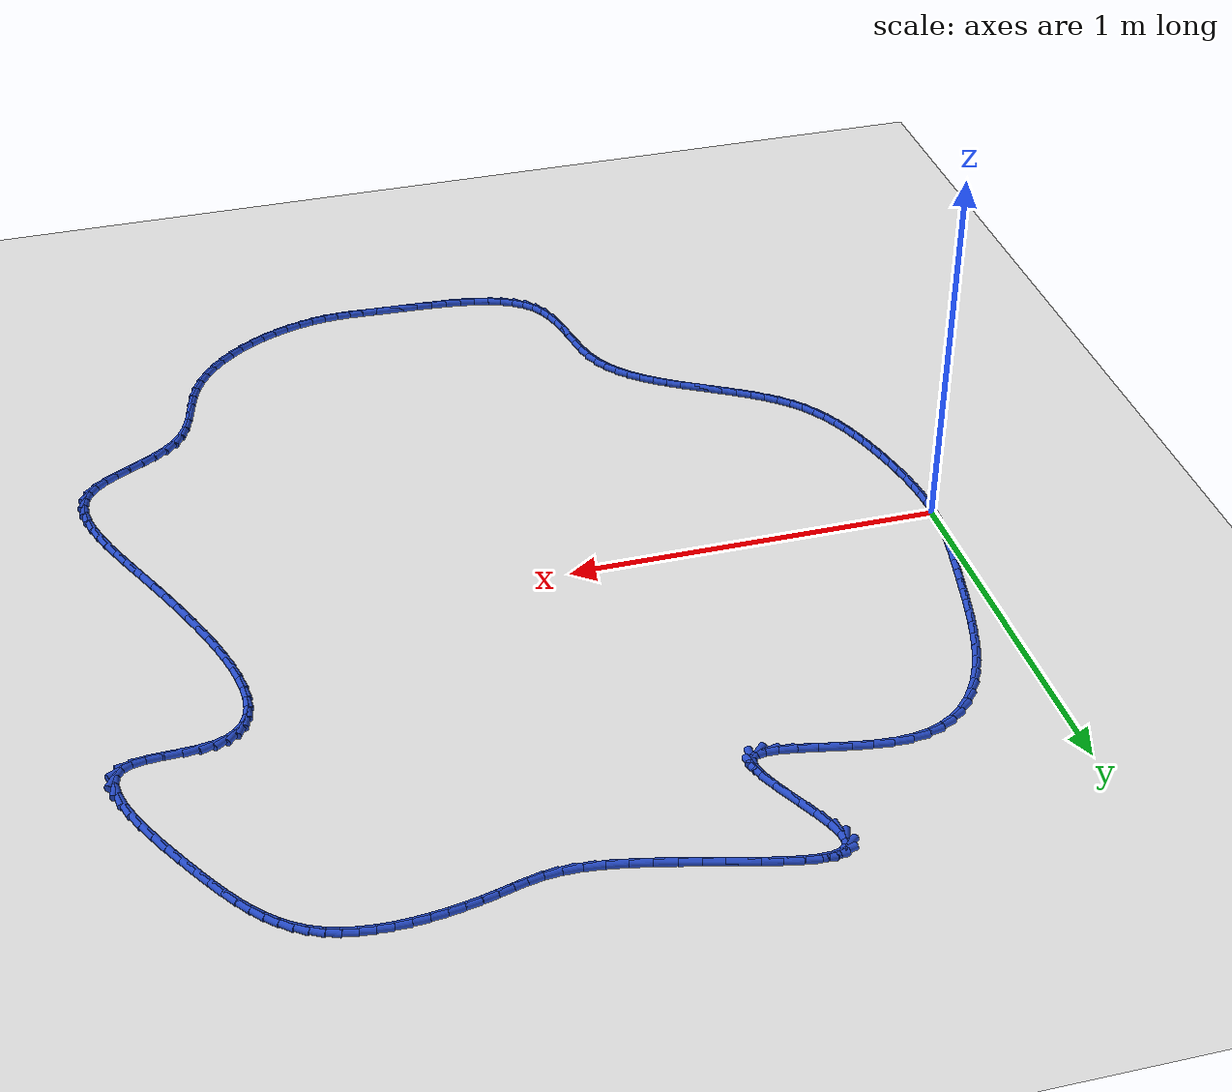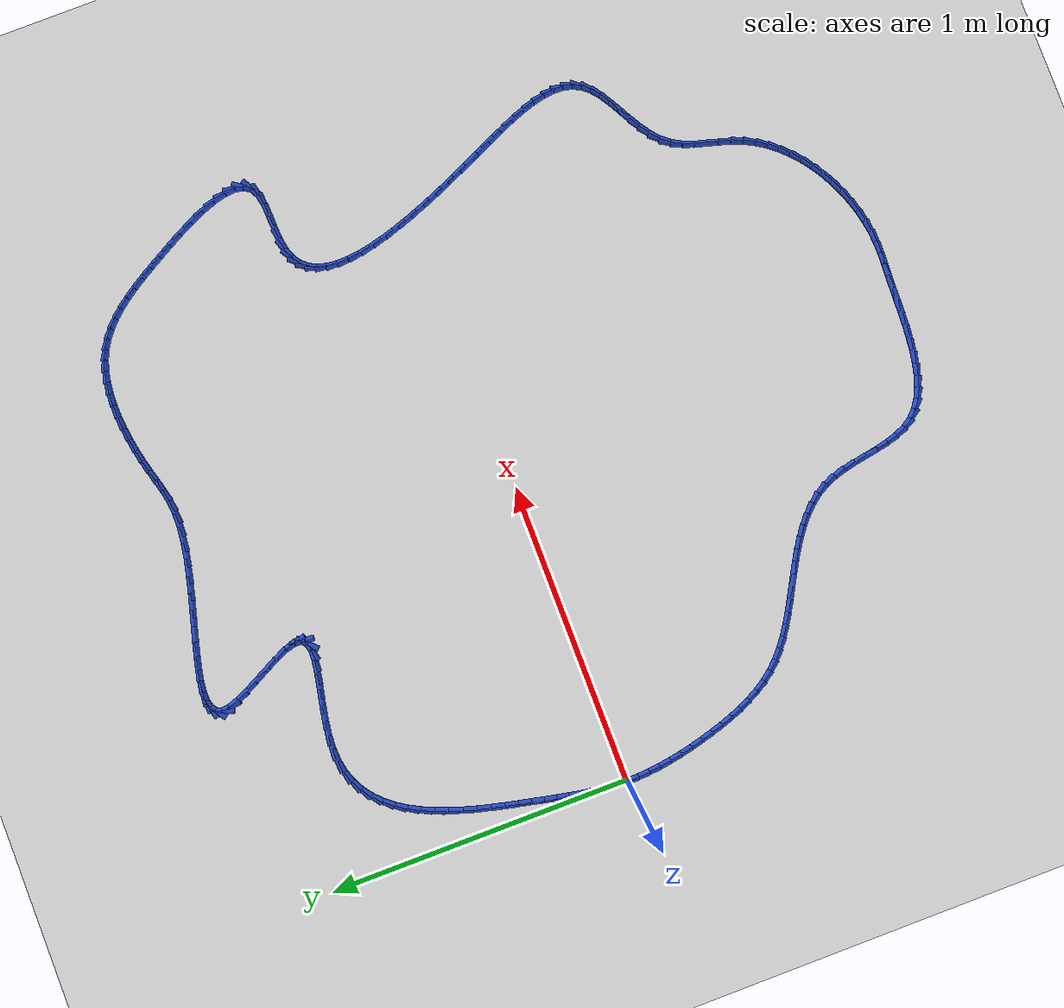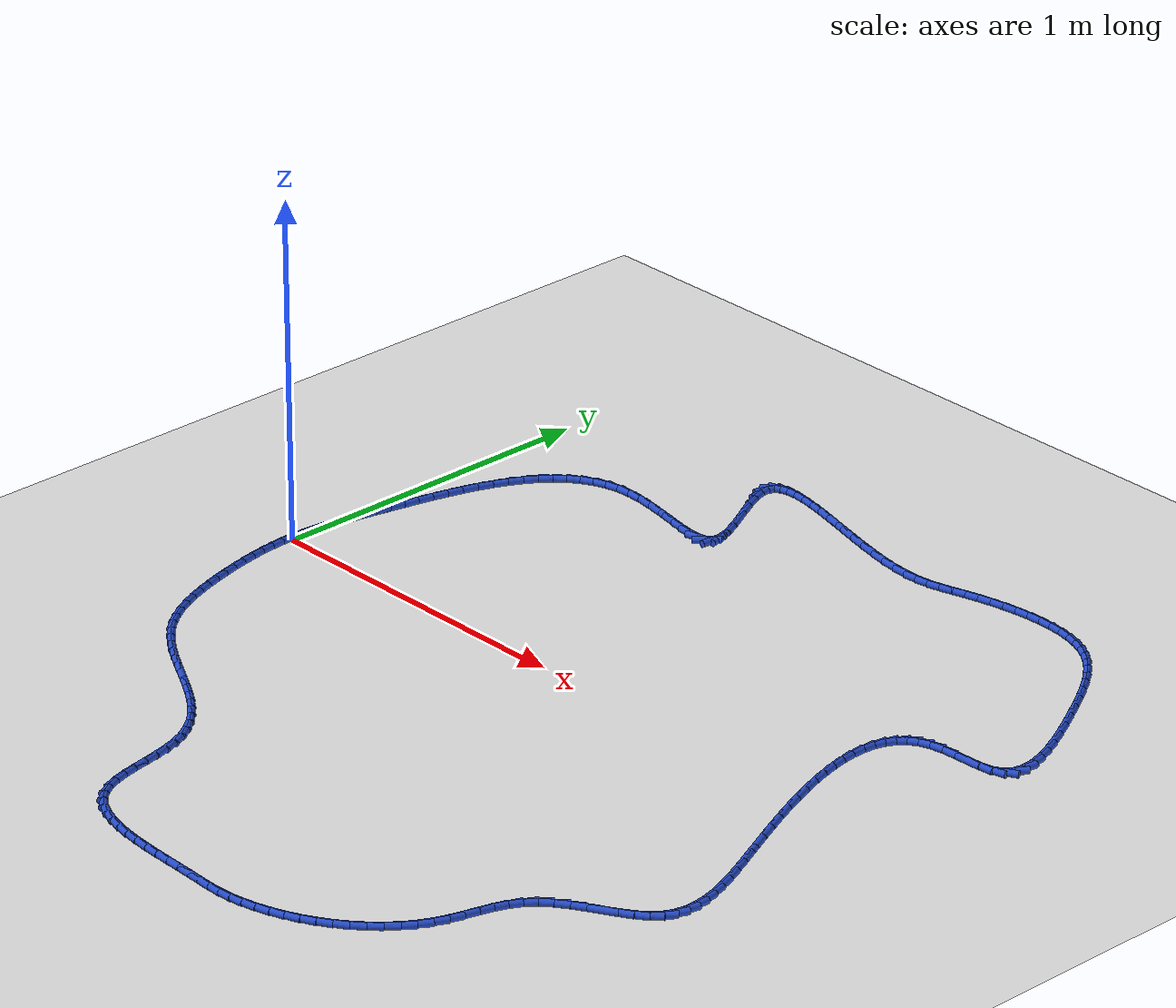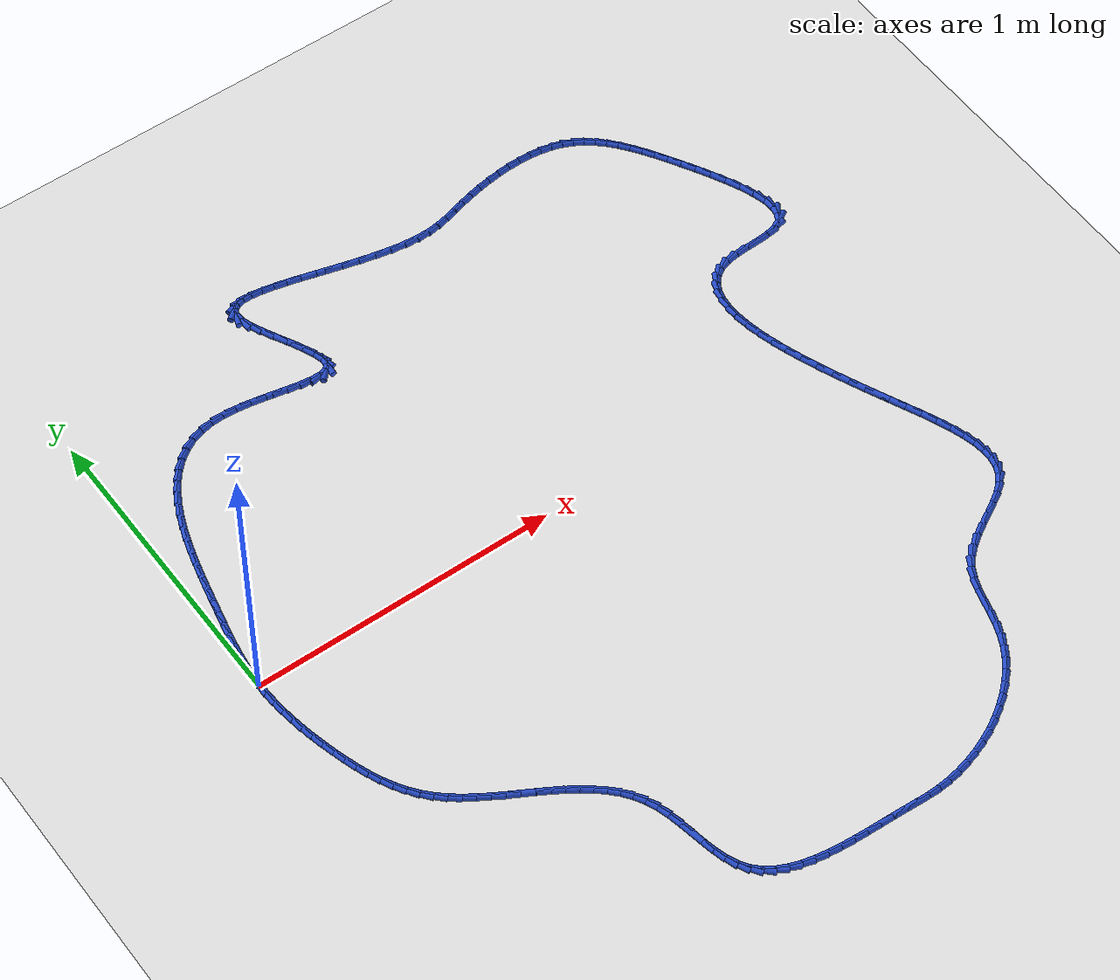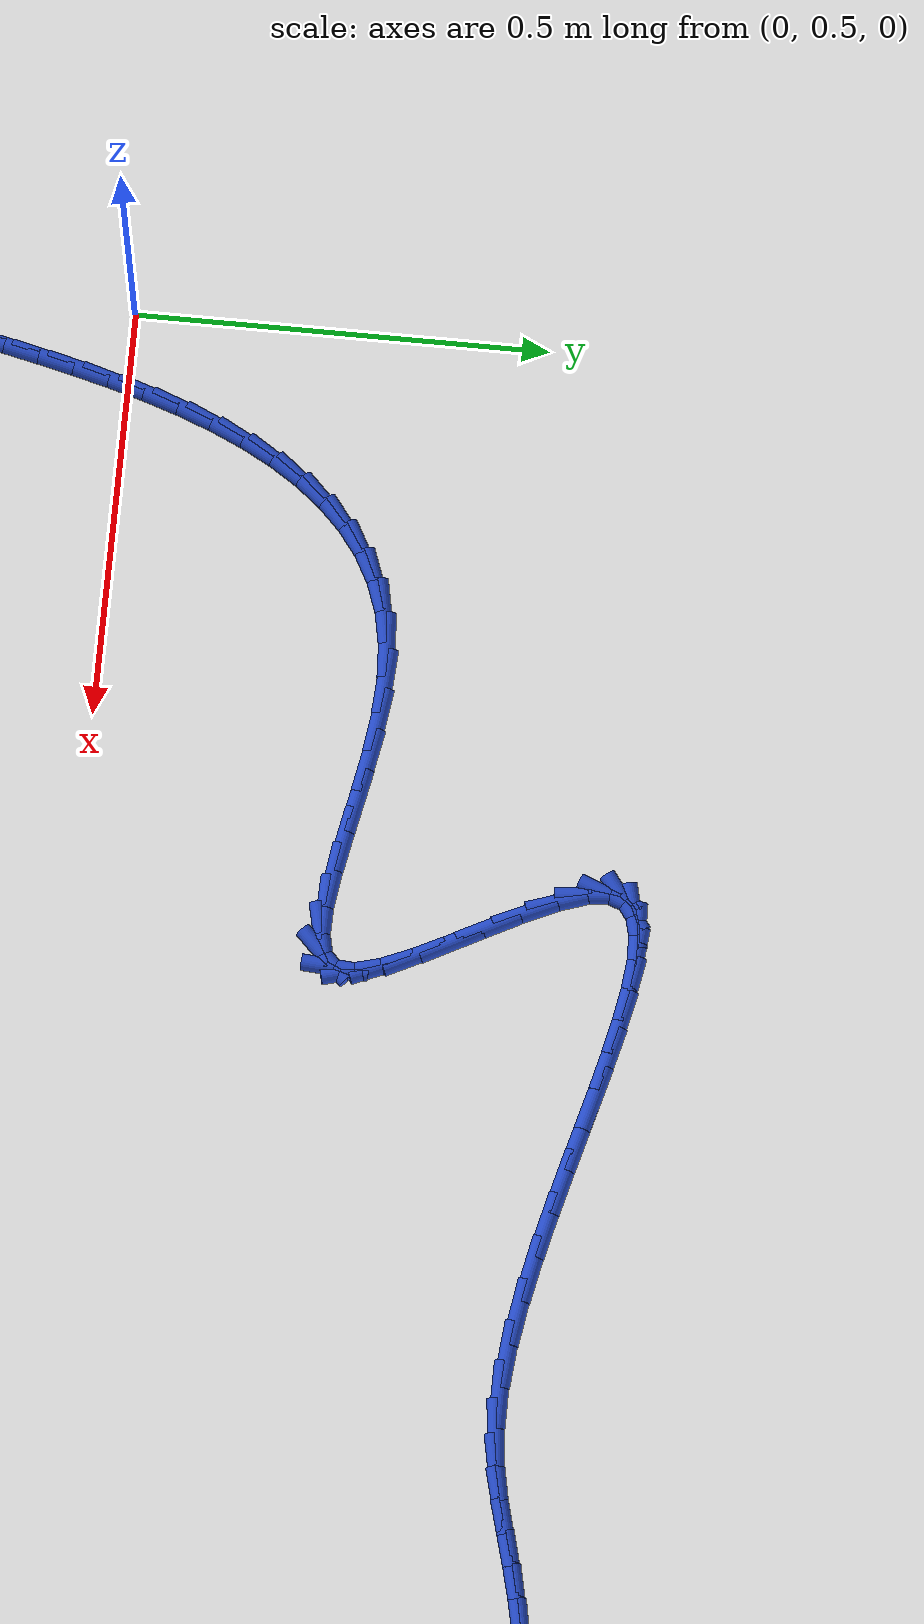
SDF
<sdf version="1.6">
 <world name="default">
  <light name="sun" type="directional">
   <pose>0 0 10 0 -0 0</pose>
   <diffuse>0.8 0.8 0.8 1</diffuse>
   <specular>0.2 0.2 0.2 1</specular>
   <attenuation>
    <range>1000</range>
    <constant>0.9</constant>
    <linear>0.01</linear>
    <quadratic>0.001</quadratic>
   </attenuation>
   <direction>-0.5 0.1 -0.9</direction>
  </light>
  <model name="ground_plane">
   <static>1</static>
   <link name="link">
    <collision name="collision">
     <geometry><plane><normal>0 0 1</normal><size>100 100</size></plane></geometry>
     <surface><friction><ode><mu>100</mu><mu2>50</mu2></ode></friction></surface>
    </collision>
    <visual name="visual">
     <cast_shadows>0</cast_shadows>
     <geometry><plane><normal>0 0 1</normal><size>100 100</size></plane></geometry>
     <material>
      <script><uri>file://media/materials/scripts/gazebo.material</uri><name>Gazebo/WhiteGlow</name></script>
     </material>
    </visual>
   </link>
  </model>
  <gravity>0 0 -9.8</gravity>
  <magnetic_field>6e-06 2.3e-05 -4.2e-05</magnetic_field>
  <atmosphere type="adiabatic"/>
  <physics name="default_physics" default="0" type="ode">
   <max_step_size>0.001</max_step_size>
   <real_time_factor>1</real_time_factor>
   <real_time_update_rate>1000</real_time_update_rate>
  </physics>
  <scene><ambient>0.4 0.4 0.4 1</ambient><background>0.7 0.7 0.7 1</background><shadows>1</shadows></scene>
  <spherical_coordinates>
   <surface_model>EARTH_WGS84</surface_model>
   <latitude_deg>0</latitude_deg>
   <longitude_deg>0</longitude_deg>
   <elevation>0</elevation>
   <heading_deg>0</heading_deg>
  </spherical_coordinates>
  <model name="line">
   <link name="link_0">
    <pose>-1.0408340855860843e-17 0.0 0.01 0 1.57 1.5338810150821318</pose>
    <collision name="collision">
     <geometry><cylinder><radius>0.01</radius><length>0.08</length></cylinder></geometry>
    </collision>
    <visual name="visual">
     <material>
      <script><name>Gazebo/Blue</name><uri>file://media/materials/scripts/gazebo.material</uri></script>
     </material>
     <geometry><cylinder><radius>0.01</radius><length>0.08</length></cylinder></geometry>
    </visual>
   </link>
   <link name="link_1">
    <pose>0.0013844145351475103 0.037485410470784825 0.01 0 1.57 1.486864023934365</pose>
    <collision name="collision">
     <geometry><cylinder><radius>0.01</radius><length>0.08</length></cylinder></geometry>
    </collision>
    <visual name="visual">
     <material>
      <script><name>Gazebo/Blue</name><uri>file://media/materials/scripts/gazebo.material</uri></script>
     </material>
     <geometry><cylinder><radius>0.01</radius><length>0.08</length></cylinder></geometry>
    </visual>
   </link>
   <link name="link_2">
    <pose>0.004524886502201455 0.07481423269260003 0.01 0 1.57 1.4466615731809624</pose>
    <collision name="collision">
     <geometry><cylinder><radius>0.01</radius><length>0.08</length></cylinder></geometry>
    </collision>
    <visual name="visual">
     <material>
      <script><name>Gazebo/Blue</name><uri>file://media/materials/scripts/gazebo.material</uri></script>
     </material>
     <geometry><cylinder><radius>0.01</radius><length>0.08</length></cylinder></geometry>
    </visual>
   </link>
   <link name="link_3">
    <pose>0.009192861250005192 0.11222497376732163 0.01 0 1.57 1.4139521590009771</pose>
    <collision name="collision">
     <geometry><cylinder><radius>0.01</radius><length>0.08</length></cylinder></geometry>
    </collision>
    <visual name="visual">
     <material>
      <script><name>Gazebo/Blue</name><uri>file://media/materials/scripts/gazebo.material</uri></script>
     </material>
     <geometry><cylinder><radius>0.01</radius><length>0.08</length></cylinder></geometry>
    </visual>
   </link>
   <link name="link_4">
    <pose>0.015159784127402091 0.1499561407968256 0.01 0 1.57 1.389035305526209</pose>
    <collision name="collision">
     <geometry><cylinder><radius>0.01</radius><length>0.08</length></cylinder></geometry>
    </collision>
    <visual name="visual">
     <material>
      <script><name>Gazebo/Blue</name><uri>file://media/materials/scripts/gazebo.material</uri></script>
     </material>
     <geometry><cylinder><radius>0.01</radius><length>0.08</length></cylinder></geometry>
    </visual>
   </link>
   <link name="link_5">
    <pose>0.02219710048323552 0.18824624088298803 0.01 0 1.57 1.3718847321204972</pose>
    <collision name="collision">
     <geometry><cylinder><radius>0.01</radius><length>0.08</length></cylinder></geometry>
    </collision>
    <visual name="visual">
     <material>
      <script><name>Gazebo/Blue</name><uri>file://media/materials/scripts/gazebo.material</uri></script>
     </material>
     <geometry><cylinder><radius>0.01</radius><length>0.08</length></cylinder></geometry>
    </visual>
   </link>
   <link name="link_6">
    <pose>0.030076255666348844 0.22733378112768488 0.01 0 1.57 1.3622171164108423</pose>
    <collision name="collision">
     <geometry><cylinder><radius>0.01</radius><length>0.08</length></cylinder></geometry>
    </collision>
    <visual name="visual">
     <material>
      <script><name>Gazebo/Blue</name><uri>file://media/materials/scripts/gazebo.material</uri></script>
     </material>
     <geometry><cylinder><radius>0.01</radius><length>0.08</length></cylinder></geometry>
    </visual>
   </link>
   <link name="link_7">
    <pose>0.03856869502558545 0.2674572686327923 0.01 0 1.57 1.3594716124734094</pose>
    <collision name="collision">
     <geometry><cylinder><radius>0.01</radius><length>0.08</length></cylinder></geometry>
    </collision>
    <visual name="visual">
     <material>
      <script><name>Gazebo/Blue</name><uri>file://media/materials/scripts/gazebo.material</uri></script>
     </material>
     <geometry><cylinder><radius>0.01</radius><length>0.08</length></cylinder></geometry>
    </visual>
   </link>
   <link name="link_8">
    <pose>0.047448762833857676 0.308850834509866 0.01 0 1.57 1.3580396451433137</pose>
    <collision name="collision">
     <geometry><cylinder><radius>0.01</radius><length>0.08</length></cylinder></geometry>
    </collision>
    <visual name="visual">
     <material>
      <script><name>Gazebo/Blue</name><uri>file://media/materials/scripts/gazebo.material</uri></script>
     </material>
     <geometry><cylinder><radius>0.01</radius><length>0.08</length></cylinder></geometry>
    </visual>
   </link>
   <link name="link_9">
    <pose>0.05666047204780515 0.3514924912209465 0.01 0 1.57 1.3502225064797304</pose>
    <collision name="collision">
     <geometry><cylinder><radius>0.01</radius><length>0.08</length></cylinder></geometry>
    </collision>
    <visual name="visual">
     <material>
      <script><name>Gazebo/Blue</name><uri>file://media/materials/scripts/gazebo.material</uri></script>
     </material>
     <geometry><cylinder><radius>0.01</radius><length>0.08</length></cylinder></geometry>
    </visual>
   </link>
   <link name="link_10">
    <pose>0.0664083976022205 0.3949669271302282 0.01 0 1.57 1.3355788204203622</pose>
    <collision name="collision">
     <geometry><cylinder><radius>0.01</radius><length>0.08</length></cylinder></geometry>
    </collision>
    <visual name="visual">
     <material>
      <script><name>Gazebo/Blue</name><uri>file://media/materials/scripts/gazebo.material</uri></script>
     </material>
     <geometry><cylinder><radius>0.01</radius><length>0.08</length></cylinder></geometry>
    </visual>
   </link>
   <link name="link_11">
    <pose>0.07691924737476162 0.43882542043267536 0.01 0 1.57 1.3139896943194462</pose>
    <collision name="collision">
     <geometry><cylinder><radius>0.01</radius><length>0.08</length></cylinder></geometry>
    </collision>
    <visual name="visual">
     <material>
      <script><name>Gazebo/Blue</name><uri>file://media/materials/scripts/gazebo.material</uri></script>
     </material>
     <geometry><cylinder><radius>0.01</radius><length>0.08</length></cylinder></geometry>
    </visual>
   </link>
   <link name="link_12">
    <pose>0.08841972924308625 0.4826192493232517 0.01 0 1.57 1.2850154068901016</pose>
    <collision name="collision">
     <geometry><cylinder><radius>0.01</radius><length>0.08</length></cylinder></geometry>
    </collision>
    <visual name="visual">
     <material>
      <script><name>Gazebo/Blue</name><uri>file://media/materials/scripts/gazebo.material</uri></script>
     </material>
     <geometry><cylinder><radius>0.01</radius><length>0.08</length></cylinder></geometry>
    </visual>
   </link>
   <link name="link_13">
    <pose>0.10113655108485224 0.5258996919969214 0.01 0 1.57 1.2479029137293958</pose>
    <collision name="collision">
     <geometry><cylinder><radius>0.01</radius><length>0.08</length></cylinder></geometry>
    </collision>
    <visual name="visual">
     <material>
      <script><name>Gazebo/Blue</name><uri>file://media/materials/scripts/gazebo.material</uri></script>
     </material>
     <geometry><cylinder><radius>0.01</radius><length>0.08</length></cylinder></geometry>
    </visual>
   </link>
   <link name="link_14">
    <pose>0.11529642077771743 0.5682180266486485 0.01 0 1.57 1.2015804053674322</pose>
    <collision name="collision">
     <geometry><cylinder><radius>0.01</radius><length>0.08</length></cylinder></geometry>
    </collision>
    <visual name="visual">
     <material>
      <script><name>Gazebo/Blue</name><uri>file://media/materials/scripts/gazebo.material</uri></script>
     </material>
     <geometry><cylinder><radius>0.01</radius><length>0.08</length></cylinder></geometry>
    </visual>
   </link>
   <link name="link_15">
    <pose>0.13112604619933962 0.6091255314733968 0.01 0 1.57 1.1446566900153725</pose>
    <collision name="collision">
     <geometry><cylinder><radius>0.01</radius><length>0.08</length></cylinder></geometry>
    </collision>
    <visual name="visual">
     <material>
      <script><name>Gazebo/Blue</name><uri>file://media/materials/scripts/gazebo.material</uri></script>
     </material>
     <geometry><cylinder><radius>0.01</radius><length>0.08</length></cylinder></geometry>
    </visual>
   </link>
   <link name="link_16">
    <pose>0.1488521352273766 0.6481734846661307 0.01 0 1.57 1.0754558614681373</pose>
    <collision name="collision">
     <geometry><cylinder><radius>0.01</radius><length>0.08</length></cylinder></geometry>
    </collision>
    <visual name="visual">
     <material>
      <script><name>Gazebo/Blue</name><uri>file://media/materials/scripts/gazebo.material</uri></script>
     </material>
     <geometry><cylinder><radius>0.01</radius><length>0.08</length></cylinder></geometry>
    </visual>
   </link>
   <link name="link_17">
    <pose>0.16870139573948623 0.684913164421814 0.01 0 1.57 0.992140794243162</pose>
    <collision name="collision">
     <geometry><cylinder><radius>0.01</radius><length>0.08</length></cylinder></geometry>
    </collision>
    <visual name="visual">
     <material>
      <script><name>Gazebo/Blue</name><uri>file://media/materials/scripts/gazebo.material</uri></script>
     </material>
     <geometry><cylinder><radius>0.01</radius><length>0.08</length></cylinder></geometry>
    </visual>
   </link>
   <link name="link_18">
    <pose>0.19090053561332632 0.7188958489354109 0.01 0 1.57 0.8930087416871463</pose>
    <collision name="collision">
     <geometry><cylinder><radius>0.01</radius><length>0.08</length></cylinder></geometry>
    </collision>
    <visual name="visual">
     <material>
      <script><name>Gazebo/Blue</name><uri>file://media/materials/scripts/gazebo.material</uri></script>
     </material>
     <geometry><cylinder><radius>0.01</radius><length>0.08</length></cylinder></geometry>
    </visual>
   </link>
   <link name="link_19">
    <pose>0.21567626272655474 0.7496728164018852 0.01 0 1.57 0.7770531894006001</pose>
    <collision name="collision">
     <geometry><cylinder><radius>0.01</radius><length>0.08</length></cylinder></geometry>
    </collision>
    <visual name="visual">
     <material>
      <script><name>Gazebo/Blue</name><uri>file://media/materials/scripts/gazebo.material</uri></script>
     </material>
     <geometry><cylinder><radius>0.01</radius><length>0.08</length></cylinder></geometry>
    </visual>
   </link>
   <link name="link_20">
    <pose>0.24325528495682924 0.7767953450162011 0.01 0 1.57 0.6448086993344256</pose>
    <collision name="collision">
     <geometry><cylinder><radius>0.01</radius><length>0.08</length></cylinder></geometry>
    </collision>
    <visual name="visual">
     <material>
      <script><name>Gazebo/Blue</name><uri>file://media/materials/scripts/gazebo.material</uri></script>
     </material>
     <geometry><cylinder><radius>0.01</radius><length>0.08</length></cylinder></geometry>
    </visual>
   </link>
   <link name="link_21">
    <pose>0.27386431018180757 0.7998147129733225 0.01 0 1.57 0.499238976755451</pose>
    <collision name="collision">
     <geometry><cylinder><radius>0.01</radius><length>0.08</length></cylinder></geometry>
    </collision>
    <visual name="visual">
     <material>
      <script><name>Gazebo/Blue</name><uri>file://media/materials/scripts/gazebo.material</uri></script>
     </material>
     <geometry><cylinder><radius>0.01</radius><length>0.08</length></cylinder></geometry>
    </visual>
   </link>
   <link name="link_22">
    <pose>0.30773004627914785 0.8182821984682137 0.01 0 1.57 0.3460576391231455</pose>
    <collision name="collision">
     <geometry><cylinder><radius>0.01</radius><length>0.08</length></cylinder></geometry>
    </collision>
    <visual name="visual">
     <material>
      <script><name>Gazebo/Blue</name><uri>file://media/materials/scripts/gazebo.material</uri></script>
     </material>
     <geometry><cylinder><radius>0.01</radius><length>0.08</length></cylinder></geometry>
    </visual>
   </link>
   <link name="link_23">
    <pose>0.3450792011265077 0.8317490796958386 0.01 0 1.57 0.1928412448394072</pose>
    <collision name="collision">
     <geometry><cylinder><radius>0.01</radius><length>0.08</length></cylinder></geometry>
    </collision>
    <visual name="visual">
     <material>
      <script><name>Gazebo/Blue</name><uri>file://media/materials/scripts/gazebo.material</uri></script>
     </material>
     <geometry><cylinder><radius>0.01</radius><length>0.08</length></cylinder></geometry>
    </visual>
   </link>
   <link name="link_24">
    <pose>0.3861384826015446 0.8397666348511607 0.01 0 1.57 0.04743158602679558</pose>
    <collision name="collision">
     <geometry><cylinder><radius>0.01</radius><length>0.08</length></cylinder></geometry>
    </collision>
    <visual name="visual">
     <material>
      <script><name>Gazebo/Blue</name><uri>file://media/materials/scripts/gazebo.material</uri></script>
     </material>
     <geometry><cylinder><radius>0.01</radius><length>0.08</length></cylinder></geometry>
    </visual>
   </link>
   <link name="link_25">
    <pose>0.43112037120265406 0.8419017986088949 0.01 0 1.57 -0.06922000271354344</pose>
    <collision name="collision">
     <geometry><cylinder><radius>0.01</radius><length>0.08</length></cylinder></geometry>
    </collision>
    <visual name="visual">
     <material>
      <script><name>Gazebo/Blue</name><uri>file://media/materials/scripts/gazebo.material</uri></script>
     </material>
     <geometry><cylinder><radius>0.01</radius><length>0.08</length></cylinder></geometry>
    </visual>
   </link>
   <link name="link_26">
    <pose>0.47948575894070256 0.8385485890944435 0.01 0 1.57 -0.14324961648170986</pose>
    <collision name="collision">
     <geometry><cylinder><radius>0.01</radius><length>0.08</length></cylinder></geometry>
    </collision>
    <visual name="visual">
     <material>
      <script><name>Gazebo/Blue</name><uri>file://media/materials/scripts/gazebo.material</uri></script>
     </material>
     <geometry><cylinder><radius>0.01</radius><length>0.08</length></cylinder></geometry>
    </visual>
   </link>
   <link name="link_27">
    <pose>0.5295857494767011 0.8313222879213649 0.01 0 1.57 -0.18520853323677097</pose>
    <collision name="collision">
     <geometry><cylinder><radius>0.01</radius><length>0.08</length></cylinder></geometry>
    </collision>
    <visual name="visual">
     <material>
      <script><name>Gazebo/Blue</name><uri>file://media/materials/scripts/gazebo.material</uri></script>
     </material>
     <geometry><cylinder><radius>0.01</radius><length>0.08</length></cylinder></geometry>
    </visual>
   </link>
   <link name="link_28">
    <pose>0.5796821503316062 0.8219364423909886 0.01 0 1.57 -0.20059339653348188</pose>
    <collision name="collision">
     <geometry><cylinder><radius>0.01</radius><length>0.08</length></cylinder></geometry>
    </collision>
    <visual name="visual">
     <material>
      <script><name>Gazebo/Blue</name><uri>file://media/materials/scripts/gazebo.material</uri></script>
     </material>
     <geometry><cylinder><radius>0.01</radius><length>0.08</length></cylinder></geometry>
    </visual>
   </link>
   <link name="link_29">
    <pose>0.6280367690263744 0.8121045998046457 0.01 0 1.57 -0.18858148281199633</pose>
    <collision name="collision">
     <geometry><cylinder><radius>0.01</radius><length>0.08</length></cylinder></geometry>
    </collision>
    <visual name="visual">
     <material>
      <script><name>Gazebo/Blue</name><uri>file://media/materials/scripts/gazebo.material</uri></script>
     </material>
     <geometry><cylinder><radius>0.01</radius><length>0.08</length></cylinder></geometry>
    </visual>
   </link>
   <link name="link_30">
    <pose>0.6729114130819626 0.8035403074636661 0.01 0 1.57 -0.13986966720312527</pose>
    <collision name="collision">
     <geometry><cylinder><radius>0.01</radius><length>0.08</length></cylinder></geometry>
    </collision>
    <visual name="visual">
     <material>
      <script><name>Gazebo/Blue</name><uri>file://media/materials/scripts/gazebo.material</uri></script>
     </material>
     <geometry><cylinder><radius>0.01</radius><length>0.08</length></cylinder></geometry>
    </visual>
   </link>
   <link name="link_31">
    <pose>0.7125678900193272 0.7979571126693802 0.01 0 1.57 -0.02716599899316748</pose>
    <collision name="collision">
     <geometry><cylinder><radius>0.01</radius><length>0.08</length></cylinder></geometry>
    </collision>
    <visual name="visual">
     <material>
      <script><name>Gazebo/Blue</name><uri>file://media/materials/scripts/gazebo.material</uri></script>
     </material>
     <geometry><cylinder><radius>0.01</radius><length>0.08</length></cylinder></geometry>
    </visual>
   </link>
   <link name="link_32">
    <pose>0.7452680073594252 0.7970685627231182 0.01 0 1.57 0.2260035886981403</pose>
    <collision name="collision">
     <geometry><cylinder><radius>0.01</radius><length>0.08</length></cylinder></geometry>
    </collision>
    <visual name="visual">
     <material>
      <script><name>Gazebo/Blue</name><uri>file://media/materials/scripts/gazebo.material</uri></script>
     </material>
     <geometry><cylinder><radius>0.01</radius><length>0.08</length></cylinder></geometry>
    </visual>
   </link>
   <link name="link_33">
    <pose>0.7692735726232129 0.8025882049262107 0.01 0 1.57 0.7879174656125562</pose>
    <collision name="collision">
     <geometry><cylinder><radius>0.01</radius><length>0.08</length></cylinder></geometry>
    </collision>
    <visual name="visual">
     <material>
      <script><name>Gazebo/Blue</name><uri>file://media/materials/scripts/gazebo.material</uri></script>
     </material>
     <geometry><cylinder><radius>0.01</radius><length>0.08</length></cylinder></geometry>
    </visual>
   </link>
   <link name="link_34">
    <pose>0.7828463933316472 0.816229586579988 0.01 0 1.57 1.4905816882147926</pose>
    <collision name="collision">
     <geometry><cylinder><radius>0.01</radius><length>0.08</length></cylinder></geometry>
    </collision>
    <visual name="visual">
     <material>
      <script><name>Gazebo/Blue</name><uri>file://media/materials/scripts/gazebo.material</uri></script>
     </material>
     <geometry><cylinder><radius>0.01</radius><length>0.08</length></cylinder></geometry>
    </visual>
   </link>
   <link name="link_35">
    <pose>0.7847014870375278 0.8393065864038246 0.01 0 1.57 -1.312764777888609</pose>
    <collision name="collision">
     <geometry><cylinder><radius>0.01</radius><length>0.08</length></cylinder></geometry>
    </collision>
    <visual name="visual">
     <material>
      <script><name>Gazebo/Blue</name><uri>file://media/materials/scripts/gazebo.material</uri></script>
     </material>
     <geometry><cylinder><radius>0.01</radius><length>0.08</length></cylinder></geometry>
    </visual>
   </link>
   <link name="link_36">
    <pose>0.7764476613049041 0.8705811604564926 0.01 0 1.57 -1.1736444867047655</pose>
    <collision name="collision">
     <geometry><cylinder><radius>0.01</radius><length>0.08</length></cylinder></geometry>
    </collision>
    <visual name="visual">
     <material>
      <script><name>Gazebo/Blue</name><uri>file://media/materials/scripts/gazebo.material</uri></script>
     </material>
     <geometry><cylinder><radius>0.01</radius><length>0.08</length></cylinder></geometry>
    </visual>
   </link>
   <link name="link_37">
    <pose>0.7608316582090342 0.9078117639020391 0.01 0 1.57 -1.111900751533667</pose>
    <collision name="collision">
     <geometry><cylinder><radius>0.01</radius><length>0.08</length></cylinder></geometry>
    </collision>
    <visual name="visual">
     <material>
      <script><name>Gazebo/Blue</name><uri>file://media/materials/scripts/gazebo.material</uri></script>
     </material>
     <geometry><cylinder><radius>0.01</radius><length>0.08</length></cylinder></geometry>
    </visual>
   </link>
   <link name="link_38">
    <pose>0.7406029404583624 0.9487544526822275 0.01 0 1.57 -1.0905657357608847</pose>
    <collision name="collision">
     <geometry><cylinder><radius>0.01</radius><length>0.08</length></cylinder></geometry>
    </collision>
    <visual name="visual">
     <material>
      <script><name>Gazebo/Blue</name><uri>file://media/materials/scripts/gazebo.material</uri></script>
     </material>
     <geometry><cylinder><radius>0.01</radius><length>0.08</length></cylinder></geometry>
    </visual>
   </link>
   <link name="link_39">
    <pose>0.7185109707613317 0.9911652827388207 0.01 0 1.57 -1.0997166024331724</pose>
    <collision name="collision">
     <geometry><cylinder><radius>0.01</radius><length>0.08</length></cylinder></geometry>
    </collision>
    <visual name="visual">
     <material>
      <script><name>Gazebo/Blue</name><uri>file://media/materials/scripts/gazebo.material</uri></script>
     </material>
     <geometry><cylinder><radius>0.01</radius><length>0.08</length></cylinder></geometry>
    </visual>
   </link>
   <link name="link_40">
    <pose>0.6973052118263865 1.0328003100135836 0.01 0 1.57 -1.1437893352278174</pose>
    <collision name="collision">
     <geometry><cylinder><radius>0.01</radius><length>0.08</length></cylinder></geometry>
    </collision>
    <visual name="visual">
     <material>
      <script><name>Gazebo/Blue</name><uri>file://media/materials/scripts/gazebo.material</uri></script>
     </material>
     <geometry><cylinder><radius>0.01</radius><length>0.08</length></cylinder></geometry>
    </visual>
   </link>
   <link name="link_41">
    <pose>0.6797351263619702 1.0714155904482792 0.01 0 1.57 -1.2472185644766596</pose>
    <collision name="collision">
     <geometry><cylinder><radius>0.01</radius><length>0.08</length></cylinder></geometry>
    </collision>
    <visual name="visual">
     <material>
      <script><name>Gazebo/Blue</name><uri>file://media/materials/scripts/gazebo.material</uri></script>
     </material>
     <geometry><cylinder><radius>0.01</radius><length>0.08</length></cylinder></geometry>
    </visual>
   </link>
   <link name="link_42">
    <pose>0.6685501770765268 1.104767179984671 0.01 0 1.57 -1.4837549612714973</pose>
    <collision name="collision">
     <geometry><cylinder><radius>0.01</radius><length>0.08</length></cylinder></geometry>
    </collision>
    <visual name="visual">
     <material>
      <script><name>Gazebo/Blue</name><uri>file://media/materials/scripts/gazebo.material</uri></script>
     </material>
     <geometry><cylinder><radius>0.01</radius><length>0.08</length></cylinder></geometry>
    </visual>
   </link>
   <link name="link_43">
    <pose>0.6662787332912858 1.1307973849179023 0.01 0 1.57 1.2076303518280236</pose>
    <collision name="collision">
     <geometry><cylinder><radius>0.01</radius><length>0.08</length></cylinder></geometry>
    </collision>
    <visual name="visual">
     <material>
      <script><name>Gazebo/Blue</name><uri>file://media/materials/scripts/gazebo.material</uri></script>
     </material>
     <geometry><cylinder><radius>0.01</radius><length>0.08</length></cylinder></geometry>
    </visual>
   </link>
   <link name="link_44">
    <pose>0.673295864148692 1.1492624641189149 0.01 0 1.57 0.6467468062849852</pose>
    <collision name="collision">
     <geometry><cylinder><radius>0.01</radius><length>0.08</length></cylinder></geometry>
    </collision>
    <visual name="visual">
     <material>
      <script><name>Gazebo/Blue</name><uri>file://media/materials/scripts/gazebo.material</uri></script>
     </material>
     <geometry><cylinder><radius>0.01</radius><length>0.08</length></cylinder></geometry>
    </visual>
   </link>
   <link name="link_45">
    <pose>0.6887627527752381 1.1609412610880783 0.01 0 1.57 0.24158050422135313</pose>
    <collision name="collision">
     <geometry><cylinder><radius>0.01</radius><length>0.08</length></cylinder></geometry>
    </collision>
    <visual name="visual">
     <material>
      <script><name>Gazebo/Blue</name><uri>file://media/materials/scripts/gazebo.material</uri></script>
     </material>
     <geometry><cylinder><radius>0.01</radius><length>0.08</length></cylinder></geometry>
    </visual>
   </link>
   <link name="link_46">
    <pose>0.7118269470503021 1.1666241057371163 0.01 0 1.57 0.016007940934466457</pose>
    <collision name="collision">
     <geometry><cylinder><radius>0.01</radius><length>0.08</length></cylinder></geometry>
    </collision>
    <visual name="visual">
     <material>
      <script><name>Gazebo/Blue</name><uri>file://media/materials/scripts/gazebo.material</uri></script>
     </material>
     <geometry><cylinder><radius>0.01</radius><length>0.08</length></cylinder></geometry>
    </visual>
   </link>
   <link name="link_47">
    <pose>0.7416359948532618 1.167101327977752 0.01 0 1.57 -0.10986147646847871</pose>
    <collision name="collision">
     <geometry><cylinder><radius>0.01</radius><length>0.08</length></cylinder></geometry>
    </collision>
    <visual name="visual">
     <material>
      <script><name>Gazebo/Blue</name><uri>file://media/materials/scripts/gazebo.material</uri></script>
     </material>
     <geometry><cylinder><radius>0.01</radius><length>0.08</length></cylinder></geometry>
    </visual>
   </link>
   <link name="link_48">
    <pose>0.7773374440634957 1.163163257721709 0.01 0 1.57 -0.18354576177938658</pose>
    <collision name="collision">
     <geometry><cylinder><radius>0.01</radius><length>0.08</length></cylinder></geometry>
    </collision>
    <visual name="visual">
     <material>
      <script><name>Gazebo/Blue</name><uri>file://media/materials/scripts/gazebo.material</uri></script>
     </material>
     <geometry><cylinder><radius>0.01</radius><length>0.08</length></cylinder></geometry>
    </visual>
   </link>
   <link name="link_49">
    <pose>0.8180788425603821 1.155600224880712 0.01 0 1.57 -0.22742128290877697</pose>
    <collision name="collision">
     <geometry><cylinder><radius>0.01</radius><length>0.08</length></cylinder></geometry>
    </collision>
    <visual name="visual">
     <material>
      <script><name>Gazebo/Blue</name><uri>file://media/materials/scripts/gazebo.material</uri></script>
     </material>
     <geometry><cylinder><radius>0.01</radius><length>0.08</length></cylinder></geometry>
    </visual>
   </link>
   <link name="link_50">
    <pose>0.8630077382232985 1.145202559366484 0.01 0 1.57 -0.2522970190864793</pose>
    <collision name="collision">
     <geometry><cylinder><radius>0.01</radius><length>0.08</length></cylinder></geometry>
    </collision>
    <visual name="visual">
     <material>
      <script><name>Gazebo/Blue</name><uri>file://media/materials/scripts/gazebo.material</uri></script>
     </material>
     <geometry><cylinder><radius>0.01</radius><length>0.08</length></cylinder></geometry>
    </visual>
   </link>
   <link name="link_51">
    <pose>0.9112716789316234 1.1327605910907488 0.01 0 1.57 -0.26360855567686203</pose>
    <collision name="collision">
     <geometry><cylinder><radius>0.01</radius><length>0.08</length></cylinder></geometry>
    </collision>
    <visual name="visual">
     <material>
      <script><name>Gazebo/Blue</name><uri>file://media/materials/scripts/gazebo.material</uri></script>
     </material>
     <geometry><cylinder><radius>0.01</radius><length>0.08</length></cylinder></geometry>
    </visual>
   </link>
   <link name="link_52">
    <pose>0.962018212564735 1.1190646499652301 0.01 0 1.57 -0.26403002023799016</pose>
    <collision name="collision">
     <geometry><cylinder><radius>0.01</radius><length>0.08</length></cylinder></geometry>
    </collision>
    <visual name="visual">
     <material>
      <script><name>Gazebo/Blue</name><uri>file://media/materials/scripts/gazebo.material</uri></script>
     </material>
     <geometry><cylinder><radius>0.01</radius><length>0.08</length></cylinder></geometry>
    </visual>
   </link>
   <link name="link_53">
    <pose>1.0143948870020116 1.1049050659016517 0.01 0 1.57 -0.2545929479313353</pose>
    <collision name="collision">
     <geometry><cylinder><radius>0.01</radius><length>0.08</length></cylinder></geometry>
    </collision>
    <visual name="visual">
     <material>
      <script><name>Gazebo/Blue</name><uri>file://media/materials/scripts/gazebo.material</uri></script>
     </material>
     <geometry><cylinder><radius>0.01</radius><length>0.08</length></cylinder></geometry>
    </visual>
   </link>
   <link name="link_54">
    <pose>1.067549250122831 1.0910721688117375 0.01 0 1.57 -0.23513124235477112</pose>
    <collision name="collision">
     <geometry><cylinder><radius>0.01</radius><length>0.08</length></cylinder></geometry>
    </collision>
    <visual name="visual">
     <material>
      <script><name>Gazebo/Blue</name><uri>file://media/materials/scripts/gazebo.material</uri></script>
     </material>
     <geometry><cylinder><radius>0.01</radius><length>0.08</length></cylinder></geometry>
    </visual>
   </link>
   <link name="link_55">
    <pose>1.1206288498065708 1.0783562886072109 0.01 0 1.57 -0.20435600917754376</pose>
    <collision name="collision">
     <geometry><cylinder><radius>0.01</radius><length>0.08</length></cylinder></geometry>
    </collision>
    <visual name="visual">
     <material>
      <script><name>Gazebo/Blue</name><uri>file://media/materials/scripts/gazebo.material</uri></script>
     </material>
     <geometry><cylinder><radius>0.01</radius><length>0.08</length></cylinder></geometry>
    </visual>
   </link>
   <link name="link_56">
    <pose>1.172781233932611 1.0675477551997958 0.01 0 1.57 -0.15964658404787332</pose>
    <collision name="collision">
     <geometry><cylinder><radius>0.01</radius><length>0.08</length></cylinder></geometry>
    </collision>
    <visual name="visual">
     <material>
      <script><name>Gazebo/Blue</name><uri>file://media/materials/scripts/gazebo.material</uri></script>
     </material>
     <geometry><cylinder><radius>0.01</radius><length>0.08</length></cylinder></geometry>
    </visual>
   </link>
   <link name="link_57">
    <pose>1.2231539503803277 1.0594368985012161 0.01 0 1.57 -0.09653172196595161</pose>
    <collision name="collision">
     <geometry><cylinder><radius>0.01</radius><length>0.08</length></cylinder></geometry>
    </collision>
    <visual name="visual">
     <material>
      <script><name>Gazebo/Blue</name><uri>file://media/materials/scripts/gazebo.material</uri></script>
     </material>
     <geometry><cylinder><radius>0.01</radius><length>0.08</length></cylinder></geometry>
    </visual>
   </link>
   <link name="link_58">
    <pose>1.2708945470290993 1.0548140484231951 0.01 0 1.57 -0.007829685031041951</pose>
    <collision name="collision">
     <geometry><cylinder><radius>0.01</radius><length>0.08</length></cylinder></geometry>
    </collision>
    <visual name="visual">
     <material>
      <script><name>Gazebo/Blue</name><uri>file://media/materials/scripts/gazebo.material</uri></script>
     </material>
     <geometry><cylinder><radius>0.01</radius><length>0.08</length></cylinder></geometry>
    </visual>
   </link>
   <link name="link_59">
    <pose>1.3151526633321604 1.054467514231139 0.01 0 1.57 0.10198420498334344</pose>
    <collision name="collision">
     <geometry><cylinder><radius>0.01</radius><length>0.08</length></cylinder></geometry>
    </collision>
    <visual name="visual">
     <material>
      <script><name>Gazebo/Blue</name><uri>file://media/materials/scripts/gazebo.material</uri></script>
     </material>
     <geometry><cylinder><radius>0.01</radius><length>0.08</length></cylinder></geometry>
    </visual>
   </link>
   <link name="link_60">
    <pose>1.3556696191958126 1.058613989263085 0.01 0 1.57 0.1953231773012431</pose>
    <collision name="collision">
     <geometry><cylinder><radius>0.01</radius><length>0.08</length></cylinder></geometry>
    </collision>
    <visual name="visual">
     <material>
      <script><name>Gazebo/Blue</name><uri>file://media/materials/scripts/gazebo.material</uri></script>
     </material>
     <geometry><cylinder><radius>0.01</radius><length>0.08</length></cylinder></geometry>
    </visual>
   </link>
   <link name="link_61">
    <pose>1.3935883825776372 1.066116050210965 0.01 0 1.57 0.2541342272450698</pose>
    <collision name="collision">
     <geometry><cylinder><radius>0.01</radius><length>0.08</length></cylinder></geometry>
    </collision>
    <visual name="visual">
     <material>
      <script><name>Gazebo/Blue</name><uri>file://media/materials/scripts/gazebo.material</uri></script>
     </material>
     <geometry><cylinder><radius>0.01</radius><length>0.08</length></cylinder></geometry>
    </visual>
   </link>
   <link name="link_62">
    <pose>1.430254888983317 1.0756401890682346 0.01 0 1.57 0.27098590067596423</pose>
    <collision name="collision">
     <geometry><cylinder><radius>0.01</radius><length>0.08</length></cylinder></geometry>
    </collision>
    <visual name="visual">
     <material>
      <script><name>Gazebo/Blue</name><uri>file://media/materials/scripts/gazebo.material</uri></script>
     </material>
     <geometry><cylinder><radius>0.01</radius><length>0.08</length></cylinder></geometry>
    </visual>
   </link>
   <link name="link_63">
    <pose>1.4670150739185377 1.08585289782835 0.01 0 1.57 0.24851708296932037</pose>
    <collision name="collision">
     <geometry><cylinder><radius>0.01</radius><length>0.08</length></cylinder></geometry>
    </collision>
    <visual name="visual">
     <material>
      <script><name>Gazebo/Blue</name><uri>file://media/materials/scripts/gazebo.material</uri></script>
     </material>
     <geometry><cylinder><radius>0.01</radius><length>0.08</length></cylinder></geometry>
    </visual>
   </link>
   <link name="link_64">
    <pose>1.50506588852211 1.0955087834785697 0.01 0 1.57 0.2128059227294861</pose>
    <collision name="collision">
     <geometry><cylinder><radius>0.01</radius><length>0.08</length></cylinder></geometry>
    </collision>
    <visual name="visual">
     <material>
      <script><name>Gazebo/Blue</name><uri>file://media/materials/scripts/gazebo.material</uri></script>
     </material>
     <geometry><cylinder><radius>0.01</radius><length>0.08</length></cylinder></geometry>
    </visual>
   </link>
   <link name="link_65">
    <pose>1.5444826091018362 1.1040258539579462 0.01 0 1.57 0.17415238583057369</pose>
    <collision name="collision">
     <geometry><cylinder><radius>0.01</radius><length>0.08</length></cylinder></geometry>
    </collision>
    <visual name="visual">
     <material>
      <script><name>Gazebo/Blue</name><uri>file://media/materials/scripts/gazebo.material</uri></script>
     </material>
     <geometry><cylinder><radius>0.01</radius><length>0.08</length></cylinder></geometry>
    </visual>
   </link>
   <link name="link_66">
    <pose>1.5848296035919973 1.1111242877561243 0.01 0 1.57 0.13150005736435066</pose>
    <collision name="collision">
     <geometry><cylinder><radius>0.01</radius><length>0.08</length></cylinder></geometry>
    </collision>
    <visual name="visual">
     <material>
      <script><name>Gazebo/Blue</name><uri>file://media/materials/scripts/gazebo.material</uri></script>
     </material>
     <geometry><cylinder><radius>0.01</radius><length>0.08</length></cylinder></geometry>
    </visual>
   </link>
   <link name="link_67">
    <pose>1.6256686496167716 1.1165257953701877 0.01 0 1.57 0.08359176729940403</pose>
    <collision name="collision">
     <geometry><cylinder><radius>0.01</radius><length>0.08</length></cylinder></geometry>
    </collision>
    <visual name="visual">
     <material>
      <script><name>Gazebo/Blue</name><uri>file://media/materials/scripts/gazebo.material</uri></script>
     </material>
     <geometry><cylinder><radius>0.01</radius><length>0.08</length></cylinder></geometry>
    </visual>
   </link>
   <link name="link_68">
    <pose>1.6665615248003414 1.1199520872972202 0.01 0 1.57 0.0289435488416422</pose>
    <collision name="collision">
     <geometry><cylinder><radius>0.01</radius><length>0.08</length></cylinder></geometry>
    </collision>
    <visual name="visual">
     <material>
      <script><name>Gazebo/Blue</name><uri>file://media/materials/scripts/gazebo.material</uri></script>
     </material>
     <geometry><cylinder><radius>0.01</radius><length>0.08</length></cylinder></geometry>
    </visual>
   </link>
   <link name="link_69">
    <pose>1.7070700067668874 1.1211248740343056 0.01 0 1.57 -0.03423075354225135</pose>
    <collision name="collision">
     <geometry><cylinder><radius>0.01</radius><length>0.08</length></cylinder></geometry>
    </collision>
    <visual name="visual">
     <material>
      <script><name>Gazebo/Blue</name><uri>file://media/materials/scripts/gazebo.material</uri></script>
     </material>
     <geometry><cylinder><radius>0.01</radius><length>0.08</length></cylinder></geometry>
    </visual>
   </link>
   <link name="link_70">
    <pose>1.7467558731405881 1.1197658660785272 0.01 0 1.57 -0.10807661653916784</pose>
    <collision name="collision">
     <geometry><cylinder><radius>0.01</radius><length>0.08</length></cylinder></geometry>
    </collision>
    <visual name="visual">
     <material>
      <script><name>Gazebo/Blue</name><uri>file://media/materials/scripts/gazebo.material</uri></script>
     </material>
     <geometry><cylinder><radius>0.01</radius><length>0.08</length></cylinder></geometry>
    </visual>
   </link>
   <link name="link_71">
    <pose>1.785180901545626 1.1155967739269688 0.01 0 1.57 -0.19509766982211882</pose>
    <collision name="collision">
     <geometry><cylinder><radius>0.01</radius><length>0.08</length></cylinder></geometry>
    </collision>
    <visual name="visual">
     <material>
      <script><name>Gazebo/Blue</name><uri>file://media/materials/scripts/gazebo.material</uri></script>
     </material>
     <geometry><cylinder><radius>0.01</radius><length>0.08</length></cylinder></geometry>
    </visual>
   </link>
   <link name="link_72">
    <pose>1.8219068696061818 1.1083393080767143 0.01 0 1.57 -0.2980091135453221</pose>
    <collision name="collision">
     <geometry><cylinder><radius>0.01</radius><length>0.08</length></cylinder></geometry>
    </collision>
    <visual name="visual">
     <material>
      <script><name>Gazebo/Blue</name><uri>file://media/materials/scripts/gazebo.material</uri></script>
     </material>
     <geometry><cylinder><radius>0.01</radius><length>0.08</length></cylinder></geometry>
    </visual>
   </link>
   <link name="link_73">
    <pose>1.8564955549464361 1.0977151790248476 0.01 0 1.57 -0.4173073700957433</pose>
    <collision name="collision">
     <geometry><cylinder><radius>0.01</radius><length>0.08</length></cylinder></geometry>
    </collision>
    <visual name="visual">
     <material>
      <script><name>Gazebo/Blue</name><uri>file://media/materials/scripts/gazebo.material</uri></script>
     </material>
     <geometry><cylinder><radius>0.01</radius><length>0.08</length></cylinder></geometry>
    </visual>
   </link>
   <link name="link_74">
    <pose>1.8885894818088 1.083486439116712 0.01 0 1.57 -0.5393908170670209</pose>
    <collision name="collision">
     <geometry><cylinder><radius>0.01</radius><length>0.08</length></cylinder></geometry>
    </collision>
    <visual name="visual">
     <material>
      <script><name>Gazebo/Blue</name><uri>file://media/materials/scripts/gazebo.material</uri></script>
     </material>
     <geometry><cylinder><radius>0.01</radius><length>0.08</length></cylinder></geometry>
    </visual>
   </link>
   <link name="link_75">
    <pose>1.9183476201681884 1.0656731623440243 0.01 0 1.57 -0.6535045213918862</pose>
    <collision name="collision">
     <geometry><cylinder><radius>0.01</radius><length>0.08</length></cylinder></geometry>
    </collision>
    <visual name="visual">
     <material>
      <script><name>Gazebo/Blue</name><uri>file://media/materials/scripts/gazebo.material</uri></script>
     </material>
     <geometry><cylinder><radius>0.01</radius><length>0.08</length></cylinder></geometry>
    </visual>
   </link>
   <link name="link_76">
    <pose>1.9461323376602966 1.044397042280193 0.01 0 1.57 -0.754750265106618</pose>
    <collision name="collision">
     <geometry><cylinder><radius>0.01</radius><length>0.08</length></cylinder></geometry>
    </collision>
    <visual name="visual">
     <material>
      <script><name>Gazebo/Blue</name><uri>file://media/materials/scripts/gazebo.material</uri></script>
     </material>
     <geometry><cylinder><radius>0.01</radius><length>0.08</length></cylinder></geometry>
    </visual>
   </link>
   <link name="link_77">
    <pose>1.9723064927104046 1.0197800177021954 0.01 0 1.57 -0.8404865064338307</pose>
    <collision name="collision">
     <geometry><cylinder><radius>0.01</radius><length>0.08</length></cylinder></geometry>
    </collision>
    <visual name="visual">
     <material>
      <script><name>Gazebo/Blue</name><uri>file://media/materials/scripts/gazebo.material</uri></script>
     </material>
     <geometry><cylinder><radius>0.01</radius><length>0.08</length></cylinder></geometry>
    </visual>
   </link>
   <link name="link_78">
    <pose>1.9972329437437935 0.9919440273870086 0.01 0 1.57 -0.9101038989665328</pose>
    <collision name="collision">
     <geometry><cylinder><radius>0.01</radius><length>0.08</length></cylinder></geometry>
    </collision>
    <visual name="visual">
     <material>
      <script><name>Gazebo/Blue</name><uri>file://media/materials/scripts/gazebo.material</uri></script>
     </material>
     <geometry><cylinder><radius>0.01</radius><length>0.08</length></cylinder></geometry>
    </visual>
   </link>
   <link name="link_79">
    <pose>2.021274549185743 0.9610110101116096 0.01 0 1.57 -0.9643595491380894</pose>
    <collision name="collision">
     <geometry><cylinder><radius>0.01</radius><length>0.08</length></cylinder></geometry>
    </collision>
    <visual name="visual">
     <material>
      <script><name>Gazebo/Blue</name><uri>file://media/materials/scripts/gazebo.material</uri></script>
     </material>
     <geometry><cylinder><radius>0.01</radius><length>0.08</length></cylinder></geometry>
    </visual>
   </link>
   <link name="link_80">
    <pose>2.0447941674615353 0.9271029046529766 0.01 0 1.57 -1.0047070122348365</pose>
    <collision name="collision">
     <geometry><cylinder><radius>0.01</radius><length>0.08</length></cylinder></geometry>
    </collision>
    <visual name="visual">
     <material>
      <script><name>Gazebo/Blue</name><uri>file://media/materials/scripts/gazebo.material</uri></script>
     </material>
     <geometry><cylinder><radius>0.01</radius><length>0.08</length></cylinder></geometry>
    </visual>
   </link>
   <link name="link_81">
    <pose>2.0681546569964495 0.8903416497880863 0.01 0 1.57 -1.0328242882978793</pose>
    <collision name="collision">
     <geometry><cylinder><radius>0.01</radius><length>0.08</length></cylinder></geometry>
    </collision>
    <visual name="visual">
     <material>
      <script><name>Gazebo/Blue</name><uri>file://media/materials/scripts/gazebo.material</uri></script>
     </material>
     <geometry><cylinder><radius>0.01</radius><length>0.08</length></cylinder></geometry>
    </visual>
   </link>
   <link name="link_82">
    <pose>2.0917188762157672 0.8508491842939158 0.01 0 1.57 -1.0503502558810145</pose>
    <collision name="collision">
     <geometry><cylinder><radius>0.01</radius><length>0.08</length></cylinder></geometry>
    </collision>
    <visual name="visual">
     <material>
      <script><name>Gazebo/Blue</name><uri>file://media/materials/scripts/gazebo.material</uri></script>
     </material>
     <geometry><cylinder><radius>0.01</radius><length>0.08</length></cylinder></geometry>
    </visual>
   </link>
   <link name="link_83">
    <pose>2.115849658332855 0.8087474628553449 0.01 0 1.57 -1.0622470371206965</pose>
    <collision name="collision">
     <geometry><cylinder><radius>0.01</radius><length>0.08</length></cylinder></geometry>
    </collision>
    <visual name="visual">
     <material>
      <script><name>Gazebo/Blue</name><uri>file://media/materials/scripts/gazebo.material</uri></script>
     </material>
     <geometry><cylinder><radius>0.01</radius><length>0.08</length></cylinder></geometry>
    </visual>
   </link>
   <link name="link_84">
    <pose>2.140595495657105 0.7643567791059349 0.01 0 1.57 -1.0815991349617615</pose>
    <collision name="collision">
     <geometry><cylinder><radius>0.01</radius><length>0.08</length></cylinder></geometry>
    </collision>
    <visual name="visual">
     <material>
      <script><name>Gazebo/Blue</name><uri>file://media/materials/scripts/gazebo.material</uri></script>
     </material>
     <geometry><cylinder><radius>0.01</radius><length>0.08</length></cylinder></geometry>
    </visual>
   </link>
   <link name="link_85">
    <pose>2.164906187762674 0.7186906662776361 0.01 0 1.57 -1.1124558007275462</pose>
    <collision name="collision">
     <geometry><cylinder><radius>0.01</radius><length>0.08</length></cylinder></geometry>
    </collision>
    <visual name="visual">
     <material>
      <script><name>Gazebo/Blue</name><uri>file://media/materials/scripts/gazebo.material</uri></script>
     </material>
     <geometry><cylinder><radius>0.01</radius><length>0.08</length></cylinder></geometry>
    </visual>
   </link>
   <link name="link_86">
    <pose>2.187491632224596 0.6729140280085125 0.01 0 1.57 -1.158308833957714</pose>
    <collision name="collision">
     <geometry><cylinder><radius>0.01</radius><length>0.08</length></cylinder></geometry>
    </collision>
    <visual name="visual">
     <material>
      <script><name>Gazebo/Blue</name><uri>file://media/materials/scripts/gazebo.material</uri></script>
     </material>
     <geometry><cylinder><radius>0.01</radius><length>0.08</length></cylinder></geometry>
    </visual>
   </link>
   <link name="link_87">
    <pose>2.207061726617905 0.6281917679366263 0.01 0 1.57 -1.2259997376130236</pose>
    <collision name="collision">
     <geometry><cylinder><radius>0.01</radius><length>0.08</length></cylinder></geometry>
    </collision>
    <visual name="visual">
     <material>
      <script><name>Gazebo/Blue</name><uri>file://media/materials/scripts/gazebo.material</uri></script>
     </material>
     <geometry><cylinder><radius>0.01</radius><length>0.08</length></cylinder></geometry>
    </visual>
   </link>
   <link name="link_88">
    <pose>2.222326368517639 0.5856887897000402 0.01 0 1.57 -1.3284806734994299</pose>
    <collision name="collision">
     <geometry><cylinder><radius>0.01</radius><length>0.08</length></cylinder></geometry>
    </collision>
    <visual name="visual">
     <material>
      <script><name>Gazebo/Blue</name><uri>file://media/materials/scripts/gazebo.material</uri></script>
     </material>
     <geometry><cylinder><radius>0.01</radius><length>0.08</length></cylinder></geometry>
    </visual>
   </link>
   <link name="link_89">
    <pose>2.2319954554988297 0.5465699969368176 0.01 0 1.57 -1.4904532015679872</pose>
    <collision name="collision">
     <geometry><cylinder><radius>0.01</radius><length>0.08</length></cylinder></geometry>
    </collision>
    <visual name="visual">
     <material>
      <script><name>Gazebo/Blue</name><uri>file://media/materials/scripts/gazebo.material</uri></script>
     </material>
     <geometry><cylinder><radius>0.01</radius><length>0.08</length></cylinder></geometry>
    </visual>
   </link>
   <link name="link_90">
    <pose>2.2347788851365133 0.5120002932850212 0.01 0 1.57 1.3860549257990797</pose>
    <collision name="collision">
     <geometry><cylinder><radius>0.01</radius><length>0.08</length></cylinder></geometry>
    </collision>
    <visual name="visual">
     <material>
      <script><name>Gazebo/Blue</name><uri>file://media/materials/scripts/gazebo.material</uri></script>
     </material>
     <geometry><cylinder><radius>0.01</radius><length>0.08</length></cylinder></geometry>
    </visual>
   </link>
   <link name="link_91">
    <pose>2.229386555005725 0.48314458238271357 0.01 0 1.57 0.9763017231322304</pose>
    <collision name="collision">
     <geometry><cylinder><radius>0.01</radius><length>0.08</length></cylinder></geometry>
    </collision>
    <visual name="visual">
     <material>
      <script><name>Gazebo/Blue</name><uri>file://media/materials/scripts/gazebo.material</uri></script>
     </material>
     <geometry><cylinder><radius>0.01</radius><length>0.08</length></cylinder></geometry>
    </visual>
   </link>
   <link name="link_92">
    <pose>2.214528362681499 0.4611677678679574 0.01 0 1.57 0.5049259371415193</pose>
    <collision name="collision">
     <geometry><cylinder><radius>0.01</radius><length>0.08</length></cylinder></geometry>
    </collision>
    <visual name="visual">
     <material>
      <script><name>Gazebo/Blue</name><uri>file://media/materials/scripts/gazebo.material</uri></script>
     </material>
     <geometry><cylinder><radius>0.01</radius><length>0.08</length></cylinder></geometry>
    </visual>
   </link>
   <link name="link_93">
    <pose>2.189077302475857 0.4471005630897749 0.01 0 1.57 0.2040438548238577</pose>
    <collision name="collision">
     <geometry><cylinder><radius>0.01</radius><length>0.08</length></cylinder></geometry>
    </collision>
    <visual name="visual">
     <material>
      <script><name>Gazebo/Blue</name><uri>file://media/materials/scripts/gazebo.material</uri></script>
     </material>
     <geometry><cylinder><radius>0.01</radius><length>0.08</length></cylinder></geometry>
    </visual>
   </link>
   <link name="link_94">
    <pose>2.1543970823412826 0.43992440935466814 0.01 0 1.57 0.07136806453644225</pose>
    <collision name="collision">
     <geometry><cylinder><radius>0.01</radius><length>0.08</length></cylinder></geometry>
    </collision>
    <visual name="visual">
     <material>
      <script><name>Gazebo/Blue</name><uri>file://media/materials/scripts/gazebo.material</uri></script>
     </material>
     <geometry><cylinder><radius>0.01</radius><length>0.08</length></cylinder></geometry>
    </visual>
   </link>
   <link name="link_95">
    <pose>2.1137948241326714 0.43702177500309786 0.01 0 1.57 0.02985365302444712</pose>
    <collision name="collision">
     <geometry><cylinder><radius>0.01</radius><length>0.08</length></cylinder></geometry>
    </collision>
    <visual name="visual">
     <material>
      <script><name>Gazebo/Blue</name><uri>file://media/materials/scripts/gazebo.material</uri></script>
     </material>
     <geometry><cylinder><radius>0.01</radius><length>0.08</length></cylinder></geometry>
    </visual>
   </link>
   <link name="link_96">
    <pose>2.0706291696561734 0.43573273956212205 0.01 0 1.57 0.05506192789850153</pose>
    <collision name="collision">
     <geometry><cylinder><radius>0.01</radius><length>0.08</length></cylinder></geometry>
    </collision>
    <visual name="visual">
     <material>
      <script><name>Gazebo/Blue</name><uri>file://media/materials/scripts/gazebo.material</uri></script>
     </material>
     <geometry><cylinder><radius>0.01</radius><length>0.08</length></cylinder></geometry>
    </visual>
   </link>
   <link name="link_97">
    <pose>2.028258760717943 0.4333973825587986 0.01 0 1.57 0.15669649025078525</pose>
    <collision name="collision">
     <geometry><cylinder><radius>0.01</radius><length>0.08</length></cylinder></geometry>
    </collision>
    <visual name="visual">
     <material>
      <script><name>Gazebo/Blue</name><uri>file://media/materials/scripts/gazebo.material</uri></script>
     </material>
     <geometry><cylinder><radius>0.01</radius><length>0.08</length></cylinder></geometry>
    </visual>
   </link>
   <link name="link_98">
    <pose>1.9900384261044752 0.4273588865234727 0.01 0 1.57 0.3494890032617733</pose>
    <collision name="collision">
     <geometry><cylinder><radius>0.01</radius><length>0.08</length></cylinder></geometry>
    </collision>
    <visual name="visual">
     <material>
      <script><name>Gazebo/Blue</name><uri>file://media/materials/scripts/gazebo.material</uri></script>
     </material>
     <geometry><cylinder><radius>0.01</radius><length>0.08</length></cylinder></geometry>
    </visual>
   </link>
   <link name="link_99">
    <pose>1.9583009386429204 0.41579217451979245 0.01 0 1.57 0.5905241538581865</pose>
    <collision name="collision">
     <geometry><cylinder><radius>0.01</radius><length>0.08</length></cylinder></geometry>
    </collision>
    <visual name="visual">
     <material>
      <script><name>Gazebo/Blue</name><uri>file://media/materials/scripts/gazebo.material</uri></script>
     </material>
     <geometry><cylinder><radius>0.01</radius><length>0.08</length></cylinder></geometry>
    </visual>
   </link>
   <link name="link_100">
    <pose>1.9329836016086293 0.39882158256115524 0.01 0 1.57 0.8499636379364107</pose>
    <collision name="collision">
     <geometry><cylinder><radius>0.01</radius><length>0.08</length></cylinder></geometry>
    </collision>
    <visual name="visual">
     <material>
      <script><name>Gazebo/Blue</name><uri>file://media/materials/scripts/gazebo.material</uri></script>
     </material>
     <geometry><cylinder><radius>0.01</radius><length>0.08</length></cylinder></geometry>
    </visual>
   </link>
   <link name="link_101">
    <pose>1.9136809676713955 0.3768503742175672 0.01 0 1.57 1.0949064885580062</pose>
    <collision name="collision">
     <geometry><cylinder><radius>0.01</radius><length>0.08</length></cylinder></geometry>
    </collision>
    <visual name="visual">
     <material>
      <script><name>Gazebo/Blue</name><uri>file://media/materials/scripts/gazebo.material</uri></script>
     </material>
     <geometry><cylinder><radius>0.01</radius><length>0.08</length></cylinder></geometry>
    </visual>
   </link>
   <link name="link_102">
    <pose>1.8999875895010114 0.35028181305903466 0.01 0 1.57 1.3015285051576626</pose>
    <collision name="collision">
     <geometry><cylinder><radius>0.01</radius><length>0.08</length></cylinder></geometry>
    </collision>
    <visual name="visual">
     <material>
      <script><name>Gazebo/Blue</name><uri>file://media/materials/scripts/gazebo.material</uri></script>
     </material>
     <geometry><cylinder><radius>0.01</radius><length>0.08</length></cylinder></geometry>
    </visual>
   </link>
   <link name="link_103">
    <pose>1.8914980197672697 0.3195191626555638 0.01 0 1.57 1.4643739545341241</pose>
    <collision name="collision">
     <geometry><cylinder><radius>0.01</radius><length>0.08</length></cylinder></geometry>
    </collision>
    <visual name="visual">
     <material>
      <script><name>Gazebo/Blue</name><uri>file://media/materials/scripts/gazebo.material</uri></script>
     </material>
     <geometry><cylinder><radius>0.01</radius><length>0.08</length></cylinder></geometry>
    </visual>
   </link>
   <link name="link_104">
    <pose>1.8878068111399626 0.28496568657716054 0.01 0 1.57 -1.5523038133422449</pose>
    <collision name="collision">
     <geometry><cylinder><radius>0.01</radius><length>0.08</length></cylinder></geometry>
    </collision>
    <visual name="visual">
     <material>
      <script><name>Gazebo/Blue</name><uri>file://media/materials/scripts/gazebo.material</uri></script>
     </material>
     <geometry><cylinder><radius>0.01</radius><length>0.08</length></cylinder></geometry>
    </visual>
   </link>
   <link name="link_105">
    <pose>1.8885085162888833 0.24702464839383131 0.01 0 1.57 -1.4567151277508343</pose>
    <collision name="collision">
     <geometry><cylinder><radius>0.01</radius><length>0.08</length></cylinder></geometry>
    </collision>
    <visual name="visual">
     <material>
      <script><name>Gazebo/Blue</name><uri>file://media/materials/scripts/gazebo.material</uri></script>
     </material>
     <geometry><cylinder><radius>0.01</radius><length>0.08</length></cylinder></geometry>
    </visual>
   </link>
   <link name="link_106">
    <pose>1.8931976878838237 0.2060993116755811 0.01 0 1.57 -1.3829239028375429</pose>
    <collision name="collision">
     <geometry><cylinder><radius>0.01</radius><length>0.08</length></cylinder></geometry>
    </collision>
    <visual name="visual">
     <material>
      <script><name>Gazebo/Blue</name><uri>file://media/materials/scripts/gazebo.material</uri></script>
     </material>
     <geometry><cylinder><radius>0.01</radius><length>0.08</length></cylinder></geometry>
    </visual>
   </link>
   <link name="link_107">
    <pose>1.901468878594577 0.16259293999241806 0.01 0 1.57 -1.325267120305898</pose>
    <collision name="collision">
     <geometry><cylinder><radius>0.01</radius><length>0.08</length></cylinder></geometry>
    </collision>
    <visual name="visual">
     <material>
      <script><name>Gazebo/Blue</name><uri>file://media/materials/scripts/gazebo.material</uri></script>
     </material>
     <geometry><cylinder><radius>0.01</radius><length>0.08</length></cylinder></geometry>
    </visual>
   </link>
   <link name="link_108">
    <pose>1.9129166410909348 0.11690879691434727 0.01 0 1.57 -1.2797012252191111</pose>
    <collision name="collision">
     <geometry><cylinder><radius>0.01</radius><length>0.08</length></cylinder></geometry>
    </collision>
    <visual name="visual">
     <material>
      <script><name>Gazebo/Blue</name><uri>file://media/materials/scripts/gazebo.material</uri></script>
     </material>
     <geometry><cylinder><radius>0.01</radius><length>0.08</length></cylinder></geometry>
    </visual>
   </link>
   <link name="link_109">
    <pose>1.927135528042691 0.069450146011375 0.01 0 1.57 -1.243380946750623</pose>
    <collision name="collision">
     <geometry><cylinder><radius>0.01</radius><length>0.08</length></cylinder></geometry>
    </collision>
    <visual name="visual">
     <material>
      <script><name>Gazebo/Blue</name><uri>file://media/materials/scripts/gazebo.material</uri></script>
     </material>
     <geometry><cylinder><radius>0.01</radius><length>0.08</length></cylinder></geometry>
    </visual>
   </link>
   <link name="link_110">
    <pose>1.9437200921196367 0.020620250853507327 0.01 0 1.57 -1.2143059100676004</pose>
    <collision name="collision">
     <geometry><cylinder><radius>0.01</radius><length>0.08</length></cylinder></geometry>
    </collision>
    <visual name="visual">
     <material>
      <script><name>Gazebo/Blue</name><uri>file://media/materials/scripts/gazebo.material</uri></script>
     </material>
     <geometry><cylinder><radius>0.01</radius><length>0.08</length></cylinder></geometry>
    </visual>
   </link>
   <link name="link_111">
    <pose>1.9622648859915657 -0.029177624989249515 0.01 0 1.57 -1.1910683563727253</pose>
    <collision name="collision">
     <geometry><cylinder><radius>0.01</radius><length>0.08</length></cylinder></geometry>
    </collision>
    <visual name="visual">
     <material>
      <script><name>Gazebo/Blue</name><uri>file://media/materials/scripts/gazebo.material</uri></script>
     </material>
     <geometry><cylinder><radius>0.01</radius><length>0.08</length></cylinder></geometry>
    </visual>
   </link>
   <link name="link_112">
    <pose>1.9823644623282703 -0.07954021794689063 0.01 0 1.57 -1.1726836822593218</pose>
    <collision name="collision">
     <geometry><cylinder><radius>0.01</radius><length>0.08</length></cylinder></geometry>
    </collision>
    <visual name="visual">
     <material>
      <script><name>Gazebo/Blue</name><uri>file://media/materials/scripts/gazebo.material</uri></script>
     </material>
     <geometry><cylinder><radius>0.01</radius><length>0.08</length></cylinder></geometry>
    </visual>
   </link>
   <link name="link_113">
    <pose>2.0036133737995425 -0.13006426444940747 0.01 0 1.57 -1.1584806898021986</pose>
    <collision name="collision">
     <geometry><cylinder><radius>0.01</radius><length>0.08</length></cylinder></geometry>
    </collision>
    <visual name="visual">
     <material>
      <script><name>Gazebo/Blue</name><uri>file://media/materials/scripts/gazebo.material</uri></script>
     </material>
     <geometry><cylinder><radius>0.01</radius><length>0.08</length></cylinder></geometry>
    </visual>
   </link>
   <link name="link_114">
    <pose>2.025606173075175 -0.1803465009267951 0.01 0 1.57 -1.1480342735790494</pose>
    <collision name="collision">
     <geometry><cylinder><radius>0.01</radius><length>0.08</length></cylinder></geometry>
    </collision>
    <visual name="visual">
     <material>
      <script><name>Gazebo/Blue</name><uri>file://media/materials/scripts/gazebo.material</uri></script>
     </material>
     <geometry><cylinder><radius>0.01</radius><length>0.08</length></cylinder></geometry>
    </visual>
   </link>
   <link name="link_115">
    <pose>2.0479374128249606 -0.22998366380904733 0.01 0 1.57 -1.1411770297406219</pose>
    <collision name="collision">
     <geometry><cylinder><radius>0.01</radius><length>0.08</length></cylinder></geometry>
    </collision>
    <visual name="visual">
     <material>
      <script><name>Gazebo/Blue</name><uri>file://media/materials/scripts/gazebo.material</uri></script>
     </material>
     <geometry><cylinder><radius>0.01</radius><length>0.08</length></cylinder></geometry>
    </visual>
   </link>
   <link name="link_116">
    <pose>2.0701997211006367 -0.27857431426374096 0.01 0 1.57 -1.1404068437084662</pose>
    <collision name="collision">
     <geometry><cylinder><radius>0.01</radius><length>0.08</length></cylinder></geometry>
    </collision>
    <visual name="visual">
     <material>
      <script><name>Gazebo/Blue</name><uri>file://media/materials/scripts/gazebo.material</uri></script>
     </material>
     <geometry><cylinder><radius>0.01</radius><length>0.08</length></cylinder></geometry>
    </visual>
   </link>
   <link name="link_117">
    <pose>2.0918859921608073 -0.3258115714410322 0.01 0 1.57 -1.150036817771369</pose>
    <collision name="collision">
     <geometry><cylinder><radius>0.01</radius><length>0.08</length></cylinder></geometry>
    </collision>
    <visual name="visual">
     <material>
      <script><name>Gazebo/Blue</name><uri>file://media/materials/scripts/gazebo.material</uri></script>
     </material>
     <geometry><cylinder><radius>0.01</radius><length>0.08</length></cylinder></geometry>
    </visual>
   </link>
   <link name="link_118">
    <pose>2.112342963696328 -0.37152712608003713 0.01 0 1.57 -1.171867779265608</pose>
    <collision name="collision">
     <geometry><cylinder><radius>0.01</radius><length>0.08</length></cylinder></geometry>
    </collision>
    <visual name="visual">
     <material>
      <script><name>Gazebo/Blue</name><uri>file://media/materials/scripts/gazebo.material</uri></script>
     </material>
     <geometry><cylinder><radius>0.01</radius><length>0.08</length></cylinder></geometry>
    </visual>
   </link>
   <link name="link_119">
    <pose>2.1309057370171605 -0.4155637014161533 0.01 0 1.57 -1.2083213083098052</pose>
    <collision name="collision">
     <geometry><cylinder><radius>0.01</radius><length>0.08</length></cylinder></geometry>
    </collision>
    <visual name="visual">
     <material>
      <script><name>Gazebo/Blue</name><uri>file://media/materials/scripts/gazebo.material</uri></script>
     </material>
     <geometry><cylinder><radius>0.01</radius><length>0.08</length></cylinder></geometry>
    </visual>
   </link>
   <link name="link_120">
    <pose>2.1469094134332685 -0.4577640206847754 0.01 0 1.57 -1.2630459326705654</pose>
    <collision name="collision">
     <geometry><cylinder><radius>0.01</radius><length>0.08</length></cylinder></geometry>
    </collision>
    <visual name="visual">
     <material>
      <script><name>Gazebo/Blue</name><uri>file://media/materials/scripts/gazebo.material</uri></script>
     </material>
     <geometry><cylinder><radius>0.01</radius><length>0.08</length></cylinder></geometry>
    </visual>
   </link>
   <link name="link_121">
    <pose>2.1596890942546123 -0.49797080712130054 0.01 0 1.57 -1.3412888273348609</pose>
    <collision name="collision">
     <geometry><cylinder><radius>0.01</radius><length>0.08</length></cylinder></geometry>
    </collision>
    <visual name="visual">
     <material>
      <script><name>Gazebo/Blue</name><uri>file://media/materials/scripts/gazebo.material</uri></script>
     </material>
     <geometry><cylinder><radius>0.01</radius><length>0.08</length></cylinder></geometry>
    </visual>
   </link>
   <link name="link_122">
    <pose>2.1685798807911567 -0.5360267839611256 0.01 0 1.57 -1.450064702859658</pose>
    <collision name="collision">
     <geometry><cylinder><radius>0.01</radius><length>0.08</length></cylinder></geometry>
    </collision>
    <visual name="visual">
     <material>
      <script><name>Gazebo/Blue</name><uri>file://media/materials/scripts/gazebo.material</uri></script>
     </material>
     <geometry><cylinder><radius>0.01</radius><length>0.08</length></cylinder></geometry>
    </visual>
   </link>
   <link name="link_123">
    <pose>2.172916874352863 -0.5717746744396468 0.01 0 1.57 1.5443112006811386</pose>
    <collision name="collision">
     <geometry><cylinder><radius>0.01</radius><length>0.08</length></cylinder></geometry>
    </collision>
    <visual name="visual">
     <material>
      <script><name>Gazebo/Blue</name><uri>file://media/materials/scripts/gazebo.material</uri></script>
     </material>
     <geometry><cylinder><radius>0.01</radius><length>0.08</length></cylinder></geometry>
    </visual>
   </link>
   <link name="link_124">
    <pose>2.1720351762496923 -0.6050572017922605 0.01 0 1.57 1.3536203823759219</pose>
    <collision name="collision">
     <geometry><cylinder><radius>0.01</radius><length>0.08</length></cylinder></geometry>
    </collision>
    <visual name="visual">
     <material>
      <script><name>Gazebo/Blue</name><uri>file://media/materials/scripts/gazebo.material</uri></script>
     </material>
     <geometry><cylinder><radius>0.01</radius><length>0.08</length></cylinder></geometry>
    </visual>
   </link>
   <link name="link_125">
    <pose>2.165269887791608 -0.6357170892543642 0.01 0 1.57 1.1252783132221909</pose>
    <collision name="collision">
     <geometry><cylinder><radius>0.01</radius><length>0.08</length></cylinder></geometry>
    </collision>
    <visual name="visual">
     <material>
      <script><name>Gazebo/Blue</name><uri>file://media/materials/scripts/gazebo.material</uri></script>
     </material>
     <geometry><cylinder><radius>0.01</radius><length>0.08</length></cylinder></geometry>
    </visual>
   </link>
   <link name="link_126">
    <pose>2.151956110288573 -0.6635970600613529 0.01 0 1.57 0.8836403954446813</pose>
    <collision name="collision">
     <geometry><cylinder><radius>0.01</radius><length>0.08</length></cylinder></geometry>
    </collision>
    <visual name="visual">
     <material>
      <script><name>Gazebo/Blue</name><uri>file://media/materials/scripts/gazebo.material</uri></script>
     </material>
     <geometry><cylinder><radius>0.01</radius><length>0.08</length></cylinder></geometry>
    </visual>
   </link>
   <link name="link_127">
    <pose>2.131473277874456 -0.6885588972956553 0.01 0 1.57 0.6900669163670313</pose>
    <collision name="collision">
     <geometry><cylinder><radius>0.01</radius><length>0.08</length></cylinder></geometry>
    </collision>
    <visual name="visual">
     <material>
      <script><name>Gazebo/Blue</name><uri>file://media/materials/scripts/gazebo.material</uri></script>
     </material>
     <geometry><cylinder><radius>0.01</radius><length>0.08</length></cylinder></geometry>
    </visual>
   </link>
   <link name="link_128">
    <pose>2.10434149622942 -0.7109547887391928 0.01 0 1.57 0.5735595070384869</pose>
    <collision name="collision">
     <geometry><cylinder><radius>0.01</radius><length>0.08</length></cylinder></geometry>
    </collision>
    <visual name="visual">
     <material>
      <script><name>Gazebo/Blue</name><uri>file://media/materials/scripts/gazebo.material</uri></script>
     </material>
     <geometry><cylinder><radius>0.01</radius><length>0.08</length></cylinder></geometry>
    </visual>
   </link>
   <link name="link_129">
    <pose>2.072293122344893 -0.7316581008970205 0.01 0 1.57 0.5150629492354584</pose>
    <collision name="collision">
     <geometry><cylinder><radius>0.01</radius><length>0.08</length></cylinder></geometry>
    </collision>
    <visual name="visual">
     <material>
      <script><name>Gazebo/Blue</name><uri>file://media/materials/scripts/gazebo.material</uri></script>
     </material>
     <geometry><cylinder><radius>0.01</radius><length>0.08</length></cylinder></geometry>
    </visual>
   </link>
   <link name="link_130">
    <pose>2.0371191786148315 -0.7515674220737467 0.01 0 1.57 0.5014594369322178</pose>
    <collision name="collision">
     <geometry><cylinder><radius>0.01</radius><length>0.08</length></cylinder></geometry>
    </collision>
    <visual name="visual">
     <material>
      <script><name>Gazebo/Blue</name><uri>file://media/materials/scripts/gazebo.material</uri></script>
     </material>
     <geometry><cylinder><radius>0.01</radius><length>0.08</length></cylinder></geometry>
    </visual>
   </link>
   <link name="link_131">
    <pose>2.0006106874331913 -0.7715813405739794 0.01 0 1.57 0.5278004237679216</pose>
    <collision name="collision">
     <geometry><cylinder><radius>0.01</radius><length>0.08</length></cylinder></geometry>
    </collision>
    <visual name="visual">
     <material>
      <script><name>Gazebo/Blue</name><uri>file://media/materials/scripts/gazebo.material</uri></script>
     </material>
     <geometry><cylinder><radius>0.01</radius><length>0.08</length></cylinder></geometry>
    </visual>
   </link>
   <link name="link_132">
    <pose>1.9645586711939271 -0.7925984447023278 0.01 0 1.57 0.5957959000685129</pose>
    <collision name="collision">
     <geometry><cylinder><radius>0.01</radius><length>0.08</length></cylinder></geometry>
    </collision>
    <visual name="visual">
     <material>
      <script><name>Gazebo/Blue</name><uri>file://media/materials/scripts/gazebo.material</uri></script>
     </material>
     <geometry><cylinder><radius>0.01</radius><length>0.08</length></cylinder></geometry>
    </visual>
   </link>
   <link name="link_133">
    <pose>1.9307541522909966 -0.815517322763399 0.01 0 1.57 0.7125931015024484</pose>
    <collision name="collision">
     <geometry><cylinder><radius>0.01</radius><length>0.08</length></cylinder></geometry>
    </collision>
    <visual name="visual">
     <material>
      <script><name>Gazebo/Blue</name><uri>file://media/materials/scripts/gazebo.material</uri></script>
     </material>
     <geometry><cylinder><radius>0.01</radius><length>0.08</length></cylinder></geometry>
    </visual>
   </link>
   <link name="link_134">
    <pose>1.9009881531183543 -0.8412365630618015 0.01 0 1.57 0.8860979342546759</pose>
    <collision name="collision">
     <geometry><cylinder><radius>0.01</radius><length>0.08</length></cylinder></geometry>
    </collision>
    <visual name="visual">
     <material>
      <script><name>Gazebo/Blue</name><uri>file://media/materials/scripts/gazebo.material</uri></script>
     </material>
     <geometry><cylinder><radius>0.01</radius><length>0.08</length></cylinder></geometry>
    </visual>
   </link>
   <link name="link_135">
    <pose>1.8769941372575836 -0.8706243592795784 0.01 0 1.57 1.0703993403243819</pose>
    <collision name="collision">
     <geometry><cylinder><radius>0.01</radius><length>0.08</length></cylinder></geometry>
    </collision>
    <visual name="visual">
     <material>
      <script><name>Gazebo/Blue</name><uri>file://media/materials/scripts/gazebo.material</uri></script>
     </material>
     <geometry><cylinder><radius>0.01</radius><length>0.08</length></cylinder></geometry>
    </visual>
   </link>
   <link name="link_136">
    <pose>1.8589055842355633 -0.9037040142914782 0.01 0 1.57 1.2029514020458636</pose>
    <collision name="collision">
     <geometry><cylinder><radius>0.01</radius><length>0.08</length></cylinder></geometry>
    </collision>
    <visual name="visual">
     <material>
      <script><name>Gazebo/Blue</name><uri>file://media/materials/scripts/gazebo.material</uri></script>
     </material>
     <geometry><cylinder><radius>0.01</radius><length>0.08</length></cylinder></geometry>
    </visual>
   </link>
   <link name="link_137">
    <pose>1.8450856527926696 -0.9395639918067675 0.01 0 1.57 1.2799290928923177</pose>
    <collision name="collision">
     <geometry><cylinder><radius>0.01</radius><length>0.08</length></cylinder></geometry>
    </collision>
    <visual name="visual">
     <material>
      <script><name>Gazebo/Blue</name><uri>file://media/materials/scripts/gazebo.material</uri></script>
     </material>
     <geometry><cylinder><radius>0.01</radius><length>0.08</length></cylinder></geometry>
    </visual>
   </link>
   <link name="link_138">
    <pose>1.8338057661717242 -0.9772443135028347 0.01 0 1.57 1.3055752548535384</pose>
    <collision name="collision">
     <geometry><cylinder><radius>0.01</radius><length>0.08</length></cylinder></geometry>
    </collision>
    <visual name="visual">
     <material>
      <script><name>Gazebo/Blue</name><uri>file://media/materials/scripts/gazebo.material</uri></script>
     </material>
     <geometry><cylinder><radius>0.01</radius><length>0.08</length></cylinder></geometry>
    </visual>
   </link>
   <link name="link_139">
    <pose>1.8233373476155512 -1.0157850010570657 0.01 0 1.57 1.2828466066888002</pose>
    <collision name="collision">
     <geometry><cylinder><radius>0.01</radius><length>0.08</length></cylinder></geometry>
    </collision>
    <visual name="visual">
     <material>
      <script><name>Gazebo/Blue</name><uri>file://media/materials/scripts/gazebo.material</uri></script>
     </material>
     <geometry><cylinder><radius>0.01</radius><length>0.08</length></cylinder></geometry>
    </visual>
   </link>
   <link name="link_140">
    <pose>1.8119518203669738 -1.0542260761468492 0.01 0 1.57 1.2117338314392252</pose>
    <collision name="collision">
     <geometry><cylinder><radius>0.01</radius><length>0.08</length></cylinder></geometry>
    </collision>
    <visual name="visual">
     <material>
      <script><name>Gazebo/Blue</name><uri>file://media/materials/scripts/gazebo.material</uri></script>
     </material>
     <geometry><cylinder><radius>0.01</radius><length>0.08</length></cylinder></geometry>
    </visual>
   </link>
   <link name="link_141">
    <pose>1.7979212224714676 -1.0916078189061338 0.01 0 1.57 1.1041742955913971</pose>
    <collision name="collision">
     <geometry><cylinder><radius>0.01</radius><length>0.08</length></cylinder></geometry>
    </collision>
    <visual name="visual">
     <material>
      <script><name>Gazebo/Blue</name><uri>file://media/materials/scripts/gazebo.material</uri></script>
     </material>
     <geometry><cylinder><radius>0.01</radius><length>0.08</length></cylinder></geometry>
    </visual>
   </link>
   <link name="link_142">
    <pose>1.7800049900485566 -1.1271754064869153 0.01 0 1.57 0.9973926744620096</pose>
    <collision name="collision">
     <geometry><cylinder><radius>0.01</radius><length>0.08</length></cylinder></geometry>
    </collision>
    <visual name="visual">
     <material>
      <script><name>Gazebo/Blue</name><uri>file://media/materials/scripts/gazebo.material</uri></script>
     </material>
     <geometry><cylinder><radius>0.01</radius><length>0.08</length></cylinder></geometry>
    </visual>
   </link>
   <link name="link_143">
    <pose>1.7583251867727538 -1.1607468503168885 0.01 0 1.57 0.898171456102067</pose>
    <collision name="collision">
     <geometry><cylinder><radius>0.01</radius><length>0.08</length></cylinder></geometry>
    </collision>
    <visual name="visual">
     <material>
      <script><name>Gazebo/Blue</name><uri>file://media/materials/scripts/gazebo.material</uri></script>
     </material>
     <geometry><cylinder><radius>0.01</radius><length>0.08</length></cylinder></geometry>
    </visual>
   </link>
   <link name="link_144">
    <pose>1.7332401740946948 -1.192239498920623 0.01 0 1.57 0.806266650258836</pose>
    <collision name="collision">
     <geometry><cylinder><radius>0.01</radius><length>0.08</length></cylinder></geometry>
    </collision>
    <visual name="visual">
     <material>
      <script><name>Gazebo/Blue</name><uri>file://media/materials/scripts/gazebo.material</uri></script>
     </material>
     <geometry><cylinder><radius>0.01</radius><length>0.08</length></cylinder></geometry>
    </visual>
   </link>
   <link name="link_145">
    <pose>1.7051083134650147 -1.2215707008226906 0.01 0 1.57 0.7210181209614073</pose>
    <collision name="collision">
     <geometry><cylinder><radius>0.01</radius><length>0.08</length></cylinder></geometry>
    </collision>
    <visual name="visual">
     <material>
      <script><name>Gazebo/Blue</name><uri>file://media/materials/scripts/gazebo.material</uri></script>
     </material>
     <geometry><cylinder><radius>0.01</radius><length>0.08</length></cylinder></geometry>
    </visual>
   </link>
   <link name="link_146">
    <pose>1.6742879663343493 -1.2486578045476586 0.01 0 1.57 0.641519313219216</pose>
    <collision name="collision">
     <geometry><cylinder><radius>0.01</radius><length>0.08</length></cylinder></geometry>
    </collision>
    <visual name="visual">
     <material>
      <script><name>Gazebo/Blue</name><uri>file://media/materials/scripts/gazebo.material</uri></script>
     </material>
     <geometry><cylinder><radius>0.01</radius><length>0.08</length></cylinder></geometry>
    </visual>
   </link>
   <link name="link_147">
    <pose>1.6411374941533339 -1.2734181586200986 0.01 0 1.57 0.5667381193527892</pose>
    <collision name="collision">
     <geometry><cylinder><radius>0.01</radius><length>0.08</length></cylinder></geometry>
    </collision>
    <visual name="visual">
     <material>
      <script><name>Gazebo/Blue</name><uri>file://media/materials/scripts/gazebo.material</uri></script>
     </material>
     <geometry><cylinder><radius>0.01</radius><length>0.08</length></cylinder></geometry>
    </visual>
   </link>
   <link name="link_148">
    <pose>1.606015258372604 -1.2957691115645802 0.01 0 1.57 0.4955895658524376</pose>
    <collision name="collision">
     <geometry><cylinder><radius>0.01</radius><length>0.08</length></cylinder></geometry>
    </collision>
    <visual name="visual">
     <material>
      <script><name>Gazebo/Blue</name><uri>file://media/materials/scripts/gazebo.material</uri></script>
     </material>
     <geometry><cylinder><radius>0.01</radius><length>0.08</length></cylinder></geometry>
    </visual>
   </link>
   <link name="link_149">
    <pose>1.5692796204427952 -1.315628011905674 0.01 0 1.57 0.42697006583724467</pose>
    <collision name="collision">
     <geometry><cylinder><radius>0.01</radius><length>0.08</length></cylinder></geometry>
    </collision>
    <visual name="visual">
     <material>
      <script><name>Gazebo/Blue</name><uri>file://media/materials/scripts/gazebo.material</uri></script>
     </material>
     <geometry><cylinder><radius>0.01</radius><length>0.08</length></cylinder></geometry>
    </visual>
   </link>
   <link name="link_150">
    <pose>1.5312889418145428 -1.3329122081679496 0.01 0 1.57 0.3597641136500781</pose>
    <collision name="collision">
     <geometry><cylinder><radius>0.01</radius><length>0.08</length></cylinder></geometry>
    </collision>
    <visual name="visual">
     <material>
      <script><name>Gazebo/Blue</name><uri>file://media/materials/scripts/gazebo.material</uri></script>
     </material>
     <geometry><cylinder><radius>0.01</radius><length>0.08</length></cylinder></geometry>
    </visual>
   </link>
   <link name="link_151">
    <pose>1.4924015839384808 -1.3475390488759773 0.01 0 1.57 0.2928321972565283</pose>
    <collision name="collision">
     <geometry><cylinder><radius>0.01</radius><length>0.08</length></cylinder></geometry>
    </collision>
    <visual name="visual">
     <material>
      <script><name>Gazebo/Blue</name><uri>file://media/materials/scripts/gazebo.material</uri></script>
     </material>
     <geometry><cylinder><radius>0.01</radius><length>0.08</length></cylinder></geometry>
    </visual>
   </link>
   <link name="link_152">
    <pose>1.4529759082652471 -1.3594258825543268 0.01 0 1.57 0.22498612008538077</pose>
    <collision name="collision">
     <geometry><cylinder><radius>0.01</radius><length>0.08</length></cylinder></geometry>
    </collision>
    <visual name="visual">
     <material>
      <script><name>Gazebo/Blue</name><uri>file://media/materials/scripts/gazebo.material</uri></script>
     </material>
     <geometry><cylinder><radius>0.01</radius><length>0.08</length></cylinder></geometry>
    </visual>
   </link>
   <link name="link_153">
    <pose>1.4133702762454763 -1.368490057727568 0.01 0 1.57 0.1549561618014813</pose>
    <collision name="collision">
     <geometry><cylinder><radius>0.01</radius><length>0.08</length></cylinder></geometry>
    </collision>
    <visual name="visual">
     <material>
      <script><name>Gazebo/Blue</name><uri>file://media/materials/scripts/gazebo.material</uri></script>
     </material>
     <geometry><cylinder><radius>0.01</radius><length>0.08</length></cylinder></geometry>
    </visual>
   </link>
   <link name="link_154">
    <pose>1.3739430493298035 -1.374648922920272 0.01 0 1.57 0.08139728968517908</pose>
    <collision name="collision">
     <geometry><cylinder><radius>0.01</radius><length>0.08</length></cylinder></geometry>
    </collision>
    <visual name="visual">
     <material>
      <script><name>Gazebo/Blue</name><uri>file://media/materials/scripts/gazebo.material</uri></script>
     </material>
     <geometry><cylinder><radius>0.01</radius><length>0.08</length></cylinder></geometry>
    </visual>
   </link>
   <link name="link_155">
    <pose>1.335050703737667 -1.37782166455769 0.01 0 1.57 0.011180247118747854</pose>
    <collision name="collision">
     <geometry><cylinder><radius>0.01</radius><length>0.08</length></cylinder></geometry>
    </collision>
    <visual name="visual">
     <material>
      <script><name>Gazebo/Blue</name><uri>file://media/materials/scripts/gazebo.material</uri></script>
     </material>
     <geometry><cylinder><radius>0.01</radius><length>0.08</length></cylinder></geometry>
    </visual>
   </link>
   <link name="link_156">
    <pose>1.2967186279889036 -1.3782502444944855 0.01 0 1.57 -0.03597085583094913</pose>
    <collision name="collision">
     <geometry><cylinder><radius>0.01</radius><length>0.08</length></cylinder></geometry>
    </collision>
    <visual name="visual">
     <material>
      <script><name>Gazebo/Blue</name><uri>file://media/materials/scripts/gazebo.material</uri></script>
     </material>
     <geometry><cylinder><radius>0.01</radius><length>0.08</length></cylinder></geometry>
    </visual>
   </link>
   <link name="link_157">
    <pose>1.2582646461494655 -1.3768664249636204 0.01 0 1.57 -0.05523471477043077</pose>
    <collision name="collision">
     <geometry><cylinder><radius>0.01</radius><length>0.08</length></cylinder></geometry>
    </collision>
    <visual name="visual">
     <material>
      <script><name>Gazebo/Blue</name><uri>file://media/materials/scripts/gazebo.material</uri></script>
     </material>
     <geometry><cylinder><radius>0.01</radius><length>0.08</length></cylinder></geometry>
    </visual>
   </link>
   <link name="link_158">
    <pose>1.2189154909465394 -1.3746907726025175 0.01 0 1.57 -0.04889128946118276</pose>
    <collision name="collision">
     <geometry><cylinder><radius>0.01</radius><length>0.08</length></cylinder></geometry>
    </collision>
    <visual name="visual">
     <material>
      <script><name>Gazebo/Blue</name><uri>file://media/materials/scripts/gazebo.material</uri></script>
     </material>
     <geometry><cylinder><radius>0.01</radius><length>0.08</length></cylinder></geometry>
    </visual>
   </link>
   <link name="link_159">
    <pose>1.1779516795309986 -1.3726864017318345 0.01 0 1.57 -0.03955507087053622</pose>
    <collision name="collision">
     <geometry><cylinder><radius>0.01</radius><length>0.08</length></cylinder></geometry>
    </collision>
    <visual name="visual">
     <material>
      <script><name>Gazebo/Blue</name><uri>file://media/materials/scripts/gazebo.material</uri></script>
     </material>
     <geometry><cylinder><radius>0.01</radius><length>0.08</length></cylinder></geometry>
    </visual>
   </link>
   <link name="link_160">
    <pose>1.1354152325733518 -1.371002991509671 0.01 0 1.57 -0.041723647693550366</pose>
    <collision name="collision">
     <geometry><cylinder><radius>0.01</radius><length>0.08</length></cylinder></geometry>
    </collision>
    <visual name="visual">
     <material>
      <script><name>Gazebo/Blue</name><uri>file://media/materials/scripts/gazebo.material</uri></script>
     </material>
     <geometry><cylinder><radius>0.01</radius><length>0.08</length></cylinder></geometry>
    </visual>
   </link>
   <link name="link_161">
    <pose>1.0919130062575857 -1.3691868659475268 0.01 0 1.57 -0.055061623474264534</pose>
    <collision name="collision">
     <geometry><cylinder><radius>0.01</radius><length>0.08</length></cylinder></geometry>
    </collision>
    <visual name="visual">
     <material>
      <script><name>Gazebo/Blue</name><uri>file://media/materials/scripts/gazebo.material</uri></script>
     </material>
     <geometry><cylinder><radius>0.01</radius><length>0.08</length></cylinder></geometry>
    </visual>
   </link>
   <link name="link_162">
    <pose>1.0480652037294913 -1.3667700918830832 0.01 0 1.57 -0.07981862206950635</pose>
    <collision name="collision">
     <geometry><cylinder><radius>0.01</radius><length>0.08</length></cylinder></geometry>
    </collision>
    <visual name="visual">
     <material>
      <script><name>Gazebo/Blue</name><uri>file://media/materials/scripts/gazebo.material</uri></script>
     </material>
     <geometry><cylinder><radius>0.01</radius><length>0.08</length></cylinder></geometry>
    </visual>
   </link>
   <link name="link_163">
    <pose>1.0044920281348586 -1.3632847361540197 0.01 0 1.57 -0.11712928415648936</pose>
    <collision name="collision">
     <geometry><cylinder><radius>0.01</radius><length>0.08</length></cylinder></geometry>
    </collision>
    <visual name="visual">
     <material>
      <script><name>Gazebo/Blue</name><uri>file://media/materials/scripts/gazebo.material</uri></script>
     </material>
     <geometry><cylinder><radius>0.01</radius><length>0.08</length></cylinder></geometry>
    </visual>
   </link>
   <link name="link_164">
    <pose>0.9618136826194774 -1.3582628655980178 0.01 0 1.57 -0.16906430596348776</pose>
    <collision name="collision">
     <geometry><cylinder><radius>0.01</radius><length>0.08</length></cylinder></geometry>
    </collision>
    <visual name="visual">
     <material>
      <script><name>Gazebo/Blue</name><uri>file://media/materials/scripts/gazebo.material</uri></script>
     </material>
     <geometry><cylinder><radius>0.01</radius><length>0.08</length></cylinder></geometry>
    </visual>
   </link>
   <link name="link_165">
    <pose>0.9206503703291392 -1.3512365470527572 0.01 0 1.57 -0.2387395624402149</pose>
    <collision name="collision">
     <geometry><cylinder><radius>0.01</radius><length>0.08</length></cylinder></geometry>
    </collision>
    <visual name="visual">
     <material>
      <script><name>Gazebo/Blue</name><uri>file://media/materials/scripts/gazebo.material</uri></script>
     </material>
     <geometry><cylinder><radius>0.01</radius><length>0.08</length></cylinder></geometry>
    </visual>
   </link>
   <link name="link_166">
    <pose>0.8816222944096344 -1.3417378473559192 0.01 0 1.57 -0.33036350428673183</pose>
    <collision name="collision">
     <geometry><cylinder><radius>0.01</radius><length>0.08</length></cylinder></geometry>
    </collision>
    <visual name="visual">
     <material>
      <script><name>Gazebo/Blue</name><uri>file://media/materials/scripts/gazebo.material</uri></script>
     </material>
     <geometry><cylinder><radius>0.01</radius><length>0.08</length></cylinder></geometry>
    </visual>
   </link>
   <link name="link_167">
    <pose>0.8453496580067525 -1.3292988333451838 0.01 0 1.57 -0.44891995796184053</pose>
    <collision name="collision">
     <geometry><cylinder><radius>0.01</radius><length>0.08</length></cylinder></geometry>
    </collision>
    <visual name="visual">
     <material>
      <script><name>Gazebo/Blue</name><uri>file://media/materials/scripts/gazebo.material</uri></script>
     </material>
     <geometry><cylinder><radius>0.01</radius><length>0.08</length></cylinder></geometry>
    </visual>
   </link>
   <link name="link_168">
    <pose>0.8124526642662845 -1.3134515718582314 0.01 0 1.57 -0.5988466251935884</pose>
    <collision name="collision">
     <geometry><cylinder><radius>0.01</radius><length>0.08</length></cylinder></geometry>
    </collision>
    <visual name="visual">
     <material>
      <script><name>Gazebo/Blue</name><uri>file://media/materials/scripts/gazebo.material</uri></script>
     </material>
     <geometry><cylinder><radius>0.01</radius><length>0.08</length></cylinder></geometry>
    </visual>
   </link>
   <link name="link_169">
    <pose>0.7835515163340201 -1.2937281297327423 0.01 0 1.57 -0.7808991015662258</pose>
    <collision name="collision">
     <geometry><cylinder><radius>0.01</radius><length>0.08</length></cylinder></geometry>
    </collision>
    <visual name="visual">
     <material>
      <script><name>Gazebo/Blue</name><uri>file://media/materials/scripts/gazebo.material</uri></script>
     </material>
     <geometry><cylinder><radius>0.01</radius><length>0.08</length></cylinder></geometry>
    </visual>
   </link>
   <link name="link_170">
    <pose>0.7592664173557494 -1.2696605738063966 0.01 0 1.57 -0.9847385166032978</pose>
    <collision name="collision">
     <geometry><cylinder><radius>0.01</radius><length>0.08</length></cylinder></geometry>
    </collision>
    <visual name="visual">
     <material>
      <script><name>Gazebo/Blue</name><uri>file://media/materials/scripts/gazebo.material</uri></script>
     </material>
     <geometry><cylinder><radius>0.01</radius><length>0.08</length></cylinder></geometry>
    </visual>
   </link>
   <link name="link_171">
    <pose>0.740137524705098 -1.240845975274539 0.01 0 1.57 -1.159756099221498</pose>
    <collision name="collision">
     <geometry><cylinder><radius>0.01</radius><length>0.08</length></cylinder></geometry>
    </collision>
    <visual name="visual">
     <material>
      <script><name>Gazebo/Blue</name><uri>file://media/materials/scripts/gazebo.material</uri></script>
     </material>
     <geometry><cylinder><radius>0.01</radius><length>0.08</length></cylinder></geometry>
    </visual>
   </link>
   <link name="link_172">
    <pose>0.7256920022992903 -1.2077040470182387 0.01 0 1.57 -1.2797320092004092</pose>
    <collision name="collision">
     <geometry><cylinder><radius>0.01</radius><length>0.08</length></cylinder></geometry>
    </collision>
    <visual name="visual">
     <material>
      <script><name>Gazebo/Blue</name><uri>file://media/materials/scripts/gazebo.material</uri></script>
     </material>
     <geometry><cylinder><radius>0.01</radius><length>0.08</length></cylinder></geometry>
    </visual>
   </link>
   <link name="link_173">
    <pose>0.7147620558352724 -1.1712188704228519 0.01 0 1.57 -1.3529585415508096</pose>
    <collision name="collision">
     <geometry><cylinder><radius>0.01</radius><length>0.08</length></cylinder></geometry>
    </collision>
    <visual name="visual">
     <material>
      <script><name>Gazebo/Blue</name><uri>file://media/materials/scripts/gazebo.material</uri></script>
     </material>
     <geometry><cylinder><radius>0.01</radius><length>0.08</length></cylinder></geometry>
    </visual>
   </link>
   <link name="link_174">
    <pose>0.706166297088258 -1.1323855663593494 0.01 0 1.57 -1.387660250723848</pose>
    <collision name="collision">
     <geometry><cylinder><radius>0.01</radius><length>0.08</length></cylinder></geometry>
    </collision>
    <visual name="visual">
     <material>
      <script><name>Gazebo/Blue</name><uri>file://media/materials/scripts/gazebo.material</uri></script>
     </material>
     <geometry><cylinder><radius>0.01</radius><length>0.08</length></cylinder></geometry>
    </visual>
   </link>
   <link name="link_175">
    <pose>0.6987233378334611 -1.092199255698701 0.01 0 1.57 -1.388559309375757</pose>
    <collision name="collision">
     <geometry><cylinder><radius>0.01</radius><length>0.08</length></cylinder></geometry>
    </collision>
    <visual name="visual">
     <material>
      <script><name>Gazebo/Blue</name><uri>file://media/materials/scripts/gazebo.material</uri></script>
     </material>
     <geometry><cylinder><radius>0.01</radius><length>0.08</length></cylinder></geometry>
    </visual>
   </link>
   <link name="link_176">
    <pose>0.6912517898460954 -1.0516550593118767 0.01 0 1.57 -1.3565897239282991</pose>
    <collision name="collision">
     <geometry><cylinder><radius>0.01</radius><length>0.08</length></cylinder></geometry>
    </collision>
    <visual name="visual">
     <material>
      <script><name>Gazebo/Blue</name><uri>file://media/materials/scripts/gazebo.material</uri></script>
     </material>
     <geometry><cylinder><radius>0.01</radius><length>0.08</length></cylinder></geometry>
    </visual>
   </link>
   <link name="link_177">
    <pose>0.6825702649013754 -1.0117480980698486 0.01 0 1.57 -1.289183593395125</pose>
    <collision name="collision">
     <geometry><cylinder><radius>0.01</radius><length>0.08</length></cylinder></geometry>
    </collision>
    <visual name="visual">
     <material>
      <script><name>Gazebo/Blue</name><uri>file://media/materials/scripts/gazebo.material</uri></script>
     </material>
     <geometry><cylinder><radius>0.01</radius><length>0.08</length></cylinder></geometry>
    </visual>
   </link>
   <link name="link_178">
    <pose>0.671497374774515 -0.9734734928435863 0.01 0 1.57 -1.1812607599073273</pose>
    <collision name="collision">
     <geometry><cylinder><radius>0.01</radius><length>0.08</length></cylinder></geometry>
    </collision>
    <visual name="visual">
     <material>
      <script><name>Gazebo/Blue</name><uri>file://media/materials/scripts/gazebo.material</uri></script>
     </material>
     <geometry><cylinder><radius>0.01</radius><length>0.08</length></cylinder></geometry>
    </visual>
   </link>
   <link name="link_179">
    <pose>0.6568607470465252 -0.9378189352930529 0.01 0 1.57 -1.0473887829742825</pose>
    <collision name="collision">
     <geometry><cylinder><radius>0.01</radius><length>0.08</length></cylinder></geometry>
    </collision>
    <visual name="visual">
     <material>
      <script><name>Gazebo/Blue</name><uri>file://media/materials/scripts/gazebo.material</uri></script>
     </material>
     <geometry><cylinder><radius>0.01</radius><length>0.08</length></cylinder></geometry>
    </visual>
   </link>
   <link name="link_180">
    <pose>0.6380834996046262 -0.9052814207125733 0.01 0 1.57 -0.9218117825718776</pose>
    <collision name="collision">
     <geometry><cylinder><radius>0.01</radius><length>0.08</length></cylinder></geometry>
    </collision>
    <visual name="visual">
     <material>
      <script><name>Gazebo/Blue</name><uri>file://media/materials/scripts/gazebo.material</uri></script>
     </material>
     <geometry><cylinder><radius>0.01</radius><length>0.08</length></cylinder></geometry>
    </visual>
   </link>
   <link name="link_181">
    <pose>0.615544567810312 -0.8755703309694409 0.01 0 1.57 -0.811969639195068</pose>
    <collision name="collision">
     <geometry><cylinder><radius>0.01</radius><length>0.08</length></cylinder></geometry>
    </collision>
    <visual name="visual">
     <material>
      <script><name>Gazebo/Blue</name><uri>file://media/materials/scripts/gazebo.material</uri></script>
     </material>
     <geometry><cylinder><radius>0.01</radius><length>0.08</length></cylinder></geometry>
    </visual>
   </link>
   <link name="link_182">
    <pose>0.5897090655982625 -0.8483240349988863 0.01 0 1.57 -0.7200052052134714</pose>
    <collision name="collision">
     <geometry><cylinder><radius>0.01</radius><length>0.08</length></cylinder></geometry>
    </collision>
    <visual name="visual">
     <material>
      <script><name>Gazebo/Blue</name><uri>file://media/materials/scripts/gazebo.material</uri></script>
     </material>
     <geometry><cylinder><radius>0.01</radius><length>0.08</length></cylinder></geometry>
    </visual>
   </link>
   <link name="link_183">
    <pose>0.561042106903157 -0.8231809017361408 0.01 0 1.57 -0.6461074007994707</pose>
    <collision name="collision">
     <geometry><cylinder><radius>0.01</radius><length>0.08</length></cylinder></geometry>
    </collision>
    <visual name="visual">
     <material>
      <script><name>Gazebo/Blue</name><uri>file://media/materials/scripts/gazebo.material</uri></script>
     </material>
     <geometry><cylinder><radius>0.01</radius><length>0.08</length></cylinder></geometry>
    </visual>
   </link>
   <link name="link_184">
    <pose>0.5300088056596765 -0.7997793001164362 0.01 0 1.57 -0.5893750040762339</pose>
    <collision name="collision">
     <geometry><cylinder><radius>0.01</radius><length>0.08</length></cylinder></geometry>
    </collision>
    <visual name="visual">
     <material>
      <script><name>Gazebo/Blue</name><uri>file://media/materials/scripts/gazebo.material</uri></script>
     </material>
     <geometry><cylinder><radius>0.01</radius><length>0.08</length></cylinder></geometry>
    </visual>
   </link>
   <link name="link_185">
    <pose>0.4970742758025 -0.7777575990750031 0.01 0 1.57 -0.5485313699369296</pose>
    <collision name="collision">
     <geometry><cylinder><radius>0.01</radius><length>0.08</length></cylinder></geometry>
    </collision>
    <visual name="visual">
     <material>
      <script><name>Gazebo/Blue</name><uri>file://media/materials/scripts/gazebo.material</uri></script>
     </material>
     <geometry><cylinder><radius>0.01</radius><length>0.08</length></cylinder></geometry>
    </visual>
   </link>
   <link name="link_186">
    <pose>0.46270363126630754 -0.7567541675470734 0.01 0 1.57 -0.5223731079174737</pose>
    <collision name="collision">
     <geometry><cylinder><radius>0.01</radius><length>0.08</length></cylinder></geometry>
    </collision>
    <visual name="visual">
     <material>
      <script><name>Gazebo/Blue</name><uri>file://media/materials/scripts/gazebo.material</uri></script>
     </material>
     <geometry><cylinder><radius>0.01</radius><length>0.08</length></cylinder></geometry>
    </visual>
   </link>
   <link name="link_187">
    <pose>0.4273619859857788 -0.7364073744678776 0.01 0 1.57 -0.5100033186152494</pose>
    <collision name="collision">
     <geometry><cylinder><radius>0.01</radius><length>0.08</length></cylinder></geometry>
    </collision>
    <visual name="visual">
     <material>
      <script><name>Gazebo/Blue</name><uri>file://media/materials/scripts/gazebo.material</uri></script>
     </material>
     <geometry><cylinder><radius>0.01</radius><length>0.08</length></cylinder></geometry>
    </visual>
   </link>
   <link name="link_188">
    <pose>0.3915144538955936 -0.7163555887726472 0.01 0 1.57 -0.5109327873102801</pose>
    <collision name="collision">
     <geometry><cylinder><radius>0.01</radius><length>0.08</length></cylinder></geometry>
    </collision>
    <visual name="visual">
     <material>
      <script><name>Gazebo/Blue</name><uri>file://media/materials/scripts/gazebo.material</uri></script>
     </material>
     <geometry><cylinder><radius>0.01</radius><length>0.08</length></cylinder></geometry>
    </visual>
   </link>
   <link name="link_189">
    <pose>0.35562614893043093 -0.696237179396613 0.01 0 1.57 -0.5251102930322759</pose>
    <collision name="collision">
     <geometry><cylinder><radius>0.01</radius><length>0.08</length></cylinder></geometry>
    </collision>
    <visual name="visual">
     <material>
      <script><name>Gazebo/Blue</name><uri>file://media/materials/scripts/gazebo.material</uri></script>
     </material>
     <geometry><cylinder><radius>0.01</radius><length>0.08</length></cylinder></geometry>
    </visual>
   </link>
   <link name="link_190">
    <pose>0.32016218502497235 -0.6756905152750072 0.01 0 1.57 -0.5529112327565451</pose>
    <collision name="collision">
     <geometry><cylinder><radius>0.01</radius><length>0.08</length></cylinder></geometry>
    </collision>
    <visual name="visual">
     <material>
      <script><name>Gazebo/Blue</name><uri>file://media/materials/scripts/gazebo.material</uri></script>
     </material>
     <geometry><cylinder><radius>0.01</radius><length>0.08</length></cylinder></geometry>
    </visual>
   </link>
   <link name="link_191">
    <pose>0.28558767611389657 -0.6543539653430603 0.01 0 1.57 -0.595084544844468</pose>
    <collision name="collision">
     <geometry><cylinder><radius>0.01</radius><length>0.08</length></cylinder></geometry>
    </collision>
    <visual name="visual">
     <material>
      <script><name>Gazebo/Blue</name><uri>file://media/materials/scripts/gazebo.material</uri></script>
     </material>
     <geometry><cylinder><radius>0.01</radius><length>0.08</length></cylinder></geometry>
    </visual>
   </link>
   <link name="link_192">
    <pose>0.25236773613188374 -0.6318658985360037 0.01 0 1.57 -0.6526306373885999</pose>
    <collision name="collision">
     <geometry><cylinder><radius>0.01</radius><length>0.08</length></cylinder></geometry>
    </collision>
    <visual name="visual">
     <material>
      <script><name>Gazebo/Blue</name><uri>file://media/materials/scripts/gazebo.material</uri></script>
     </material>
     <geometry><cylinder><radius>0.01</radius><length>0.08</length></cylinder></geometry>
    </visual>
   </link>
   <link name="link_193">
    <pose>0.2209674790136135 -0.6078646837890688 0.01 0 1.57 -0.7265576182838007</pose>
    <collision name="collision">
     <geometry><cylinder><radius>0.01</radius><length>0.08</length></cylinder></geometry>
    </collision>
    <visual name="visual">
     <material>
      <script><name>Gazebo/Blue</name><uri>file://media/materials/scripts/gazebo.material</uri></script>
     </material>
     <geometry><cylinder><radius>0.01</radius><length>0.08</length></cylinder></geometry>
    </visual>
   </link>
   <link name="link_194">
    <pose>0.19185201869376567 -0.5819886900374868 0.01 0 1.57 -0.8173021437911109</pose>
    <collision name="collision">
     <geometry><cylinder><radius>0.01</radius><length>0.08</length></cylinder></geometry>
    </collision>
    <visual name="visual">
     <material>
      <script><name>Gazebo/Blue</name><uri>file://media/materials/scripts/gazebo.material</uri></script>
     </material>
     <geometry><cylinder><radius>0.01</radius><length>0.08</length></cylinder></geometry>
    </visual>
   </link>
   <link name="link_195">
    <pose>0.16548214282638812 -0.5538801457730083 0.01 0 1.57 -0.9149070073317634</pose>
    <collision name="collision">
     <geometry><cylinder><radius>0.01</radius><length>0.08</length></cylinder></geometry>
    </collision>
    <visual name="visual">
     <material>
      <script><name>Gazebo/Blue</name><uri>file://media/materials/scripts/gazebo.material</uri></script>
     </material>
     <geometry><cylinder><radius>0.01</radius><length>0.08</length></cylinder></geometry>
    </visual>
   </link>
   <link name="link_196">
    <pose>0.14204560661946827 -0.5234248568802925 0.01 0 1.57 -1.003091259931415</pose>
    <collision name="collision">
     <geometry><cylinder><radius>0.01</radius><length>0.08</length></cylinder></geometry>
    </collision>
    <visual name="visual">
     <material>
      <script><name>Gazebo/Blue</name><uri>file://media/materials/scripts/gazebo.material</uri></script>
     </material>
     <geometry><cylinder><radius>0.01</radius><length>0.08</length></cylinder></geometry>
    </visual>
   </link>
   <link name="link_197">
    <pose>0.12129904115972354 -0.4908932432010389 0.01 0 1.57 -1.079869448055332</pose>
    <collision name="collision">
     <geometry><cylinder><radius>0.01</radius><length>0.08</length></cylinder></geometry>
    </collision>
    <visual name="visual">
     <material>
      <script><name>Gazebo/Blue</name><uri>file://media/materials/scripts/gazebo.material</uri></script>
     </material>
     <geometry><cylinder><radius>0.01</radius><length>0.08</length></cylinder></geometry>
    </visual>
   </link>
   <link name="link_198">
    <pose>0.10296104975912516 -0.45658964987177403 0.01 0 1.57 -1.1453008507867803</pose>
    <collision name="collision">
     <geometry><cylinder><radius>0.01</radius><length>0.08</length></cylinder></geometry>
    </collision>
    <visual name="visual">
     <material>
      <script><name>Gazebo/Blue</name><uri>file://media/materials/scripts/gazebo.material</uri></script>
     </material>
     <geometry><cylinder><radius>0.01</radius><length>0.08</length></cylinder></geometry>
    </visual>
   </link>
   <link name="link_199">
    <pose>0.08675023572964487 -0.4208184220290253 0.01 0 1.57 -1.1998671746621121</pose>
    <collision name="collision">
     <geometry><cylinder><radius>0.01</radius><length>0.08</length></cylinder></geometry>
    </collision>
    <visual name="visual">
     <material>
      <script><name>Gazebo/Blue</name><uri>file://media/materials/scripts/gazebo.material</uri></script>
     </material>
     <geometry><cylinder><radius>0.01</radius><length>0.08</length></cylinder></geometry>
    </visual>
   </link>
   <link name="link_200">
    <pose>0.07238520238325444 -0.3838839048093199 0.01 0 1.57 -1.244223479703674</pose>
    <collision name="collision">
     <geometry><cylinder><radius>0.01</radius><length>0.08</length></cylinder></geometry>
    </collision>
    <visual name="visual">
     <material>
      <script><name>Gazebo/Blue</name><uri>file://media/materials/scripts/gazebo.material</uri></script>
     </material>
     <geometry><cylinder><radius>0.01</radius><length>0.08</length></cylinder></geometry>
    </visual>
   </link>
   <link name="link_201">
    <pose>0.0595845530319256 -0.34609044334918504 0.01 0 1.57 -1.279022718670905</pose>
    <collision name="collision">
     <geometry><cylinder><radius>0.01</radius><length>0.08</length></cylinder></geometry>
    </collision>
    <visual name="visual">
     <material>
      <script><name>Gazebo/Blue</name><uri>file://media/materials/scripts/gazebo.material</uri></script>
     </material>
     <geometry><cylinder><radius>0.01</radius><length>0.08</length></cylinder></geometry>
    </visual>
   </link>
   <link name="link_202">
    <pose>0.04806689098762984 -0.30774238278514693 0.01 0 1.57 -1.3053726801272243</pose>
    <collision name="collision">
     <geometry><cylinder><radius>0.01</radius><length>0.08</length></cylinder></geometry>
    </collision>
    <visual name="visual">
     <material>
      <script><name>Gazebo/Blue</name><uri>file://media/materials/scripts/gazebo.material</uri></script>
     </material>
     <geometry><cylinder><radius>0.01</radius><length>0.08</length></cylinder></geometry>
    </visual>
   </link>
   <link name="link_203">
    <pose>0.0375713374873838 -0.2691327161191194 0.01 0 1.57 -1.330325500494913</pose>
    <collision name="collision">
     <geometry><cylinder><radius>0.01</radius><length>0.08</length></cylinder></geometry>
    </collision>
    <visual name="visual">
     <material>
      <script><name>Gazebo/Blue</name><uri>file://media/materials/scripts/gazebo.material</uri></script>
     </material>
     <geometry><cylinder><radius>0.01</radius><length>0.08</length></cylinder></geometry>
    </visual>
   </link>
   <link name="link_204">
    <pose>0.028078562809816084 -0.23042079236948762 0.01 0 1.57 -1.3584641786401253</pose>
    <collision name="collision">
     <geometry><cylinder><radius>0.01</radius><length>0.08</length></cylinder></geometry>
    </collision>
    <visual name="visual">
     <material>
      <script><name>Gazebo/Blue</name><uri>file://media/materials/scripts/gazebo.material</uri></script>
     </material>
     <geometry><cylinder><radius>0.01</radius><length>0.08</length></cylinder></geometry>
    </visual>
   </link>
   <link name="link_205">
    <pose>0.0197265253699004 -0.1916789363505176 0.01 0 1.57 -1.3900895905732087</pose>
    <collision name="collision">
     <geometry><cylinder><radius>0.01</radius><length>0.08</length></cylinder></geometry>
    </collision>
    <visual name="visual">
     <material>
      <script><name>Gazebo/Blue</name><uri>file://media/materials/scripts/gazebo.material</uri></script>
     </material>
     <geometry><cylinder><radius>0.01</radius><length>0.08</length></cylinder></geometry>
    </visual>
   </link>
   <link name="link_206">
    <pose>0.012655870975205255 -0.15297798599890677 0.01 0 1.57 -1.4254501744800194</pose>
    <collision name="collision">
     <geometry><cylinder><radius>0.01</radius><length>0.08</length></cylinder></geometry>
    </collision>
    <visual name="visual">
     <material>
      <script><name>Gazebo/Blue</name><uri>file://media/materials/scripts/gazebo.material</uri></script>
     </material>
     <geometry><cylinder><radius>0.01</radius><length>0.08</length></cylinder></geometry>
    </visual>
   </link>
   <link name="link_207">
    <pose>0.007007245433299132 -0.11438877925135223 0.01 0 1.57 -1.4648083723929024</pose>
    <collision name="collision">
     <geometry><cylinder><radius>0.01</radius><length>0.08</length></cylinder></geometry>
    </collision>
    <visual name="visual">
     <material>
      <script><name>Gazebo/Blue</name><uri>file://media/materials/scripts/gazebo.material</uri></script>
     </material>
     <geometry><cylinder><radius>0.01</radius><length>0.08</length></cylinder></geometry>
    </visual>
   </link>
   <link name="link_208">
    <pose>0.0029212945517505516 -0.07598215404455141 0.01 0 1.57 -1.5084282958277124</pose>
    <collision name="collision">
     <geometry><cylinder><radius>0.01</radius><length>0.08</length></cylinder></geometry>
    </collision>
    <visual name="visual">
     <material>
      <script><name>Gazebo/Blue</name><uri>file://media/materials/scripts/gazebo.material</uri></script>
     </material>
     <geometry><cylinder><radius>0.01</radius><length>0.08</length></cylinder></geometry>
    </visual>
   </link>
   <link name="link_209">
    <pose>0.0005386641381279703 -0.03782894831520067 0.01 0 1.57 -1.5565578200537105</pose>
    <collision name="collision">
     <geometry><cylinder><radius>0.01</radius><length>0.08</length></cylinder></geometry>
    </collision>
    <visual name="visual">
     <material>
      <script><name>Gazebo/Blue</name><uri>file://media/materials/scripts/gazebo.material</uri></script>
     </material>
     <geometry><cylinder><radius>0.01</radius><length>0.08</length></cylinder></geometry>
    </visual>
   </link>
   <link name="link_210">
    <pose>-6.938893903907228e-18 -9.020562075079397e-17 0.01 0 1.57 1.5321887739206883</pose>
    <collision name="collision">
     <geometry><cylinder><radius>0.01</radius><length>0.08</length></cylinder></geometry>
    </collision>
    <visual name="visual">
     <material>
      <script><name>Gazebo/Blue</name><uri>file://media/materials/scripts/gazebo.material</uri></script>
     </material>
     <geometry><cylinder><radius>0.01</radius><length>0.08</length></cylinder></geometry>
    </visual>
   </link>
   <link name="link_211">
    <pose>0.0014459479449350238 0.03743385296435571 0.01 0 1.57 1.4744923232719287</pose>
    <collision name="collision">
     <geometry><cylinder><radius>0.01</radius><length>0.08</length></cylinder></geometry>
    </collision>
    <visual name="visual">
     <material>
      <script><name>Gazebo/Blue</name><uri>file://media/materials/scripts/gazebo.material</uri></script>
     </material>
     <geometry><cylinder><radius>0.01</radius><length>0.08</length></cylinder></geometry>
    </visual>
   </link>
   <link name="link_212">
    <pose>0.005017153780501814 0.07440177264117029 0.01 0 1.57 1.5034650046630276</pose>
    <collision name="collision">
     <geometry><cylinder><radius>0.01</radius><length>0.08</length></cylinder></geometry>
    </collision>
    <visual name="visual">
     <material>
      <script><name>Gazebo/Blue</name><uri>file://media/materials/scripts/gazebo.material</uri></script>
     </material>
     <geometry><cylinder><radius>0.01</radius><length>0.08</length></cylinder></geometry>
    </visual>
   </link>
  </model>
 </world>
</sdf>
